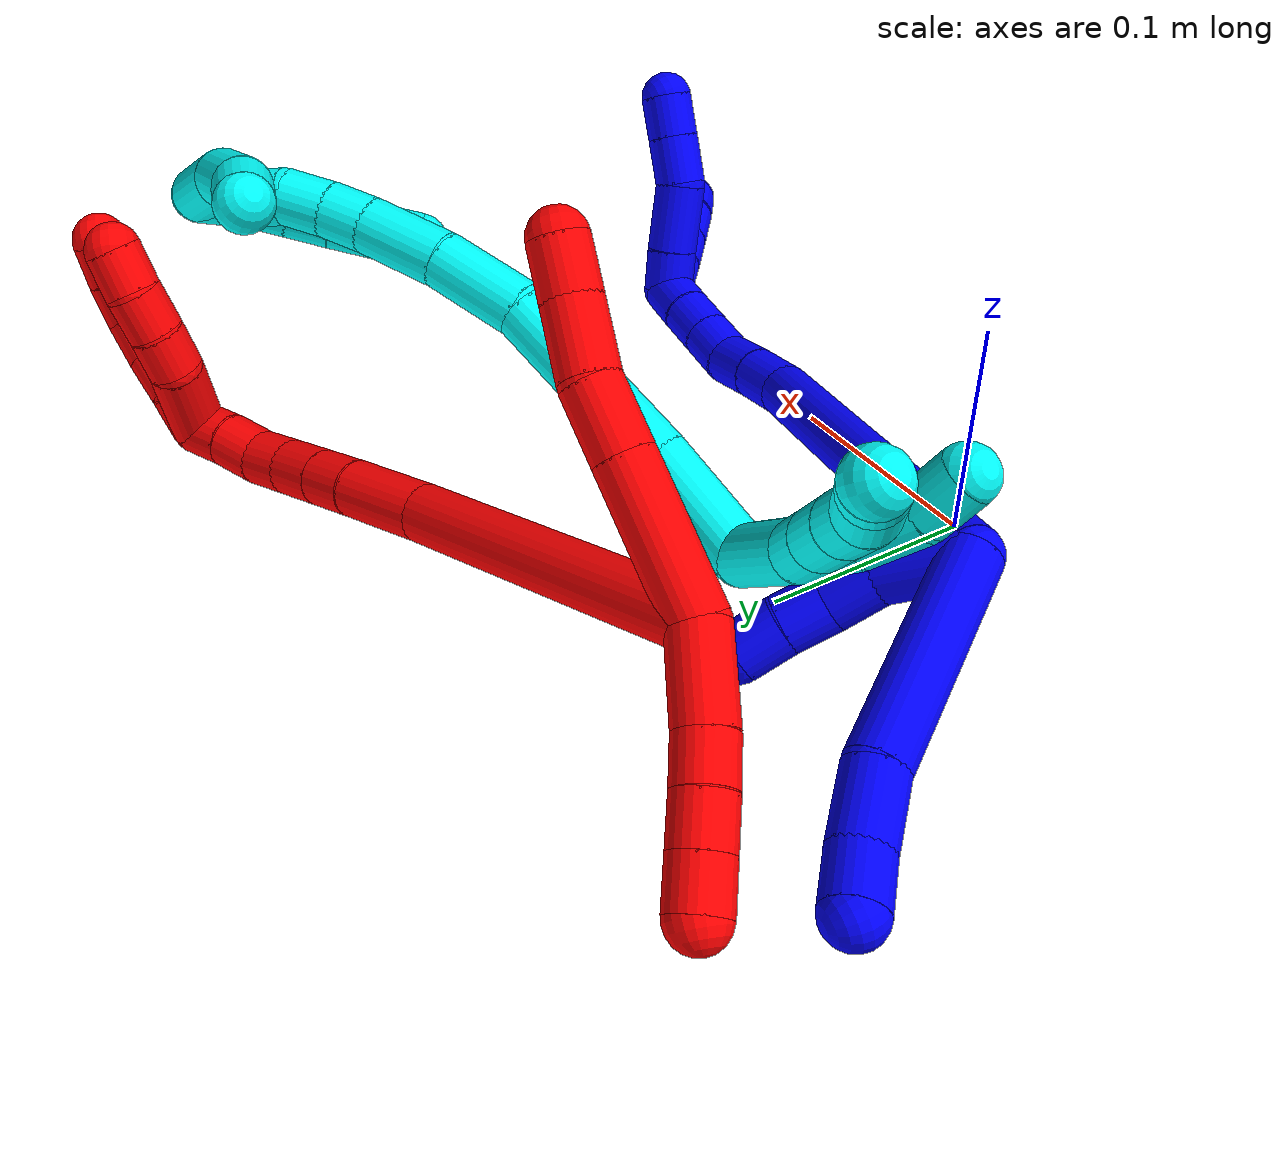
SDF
<sdf version="1.7">
 <world name="default">
  <plugin name="TubeGeneratorPlugin" filename="libtube_generator_plugin.so"/>
  <model name="photoneo_s_sensor">
   <static>1</static>
   <pose>0 0 2 1.57079 1.57079 3.14159</pose>
   <link name="link">
    <inertial><mass>0.1</mass></inertial>
    <sensor name="sensor" type="depth">
     <update_rate>30</update_rate>
     <camera>
      <horizontal_fov>1.22</horizontal_fov>
      <image><width>1920</width><height>1200</height><format>B8G8R8</format></image>
      <clip><near>0.1</near><far>4</far></clip>
      <depth_camera><output>points</output></depth_camera>
     </camera>
     <plugin name="camera_plugin" filename="libgazebo_ros_depth_camera.so">
      <baseline>0.2</baseline>
      <alwaysOn>1</alwaysOn>
      <updateRate>0.0</updateRate>
      <cameraName>camera_ir</cameraName>
      <imageTopicName>/camera/color/image_raw</imageTopicName>
      <cameraInfoTopicName>/camera/color/camera_info</cameraInfoTopicName>
      <depthImageTopicName>/camera/depth/image_raw</depthImageTopicName>
      <depthImageCameraInfoTopicName>/camera/depth/camera_info</depthImageCameraInfoTopicName>
      <pointCloudTopicName>/camera/depth/points</pointCloudTopicName>
      <frameName>fr_optical</frameName>
      <pointCloudCutoff>0.1</pointCloudCutoff>
      <pointCloudCutoffMax>2.0</pointCloudCutoffMax>
      <distortionK1>0</distortionK1>
      <distortionK2>0</distortionK2>
      <distortionK3>0</distortionK3>
      <distortionT1>0</distortionT1>
      <distortionT2>0</distortionT2>
      <CxPrime>0</CxPrime>
      <Cx>0</Cx>
      <Cy>0</Cy>
      <focalLength>0</focalLength>
      <hackBaseline>0</hackBaseline>
     </plugin>
    </sensor>
   </link>
  </model>
  <gravity>0 0 -9.8</gravity>
  <magnetic_field>6e-06 2.3e-05 -4.2e-05</magnetic_field>
  <atmosphere type="adiabatic"/>
  <physics name="default_physics" default="0" type="ode">
   <max_step_size>0.003</max_step_size>
   <real_time_factor>1</real_time_factor>
   <real_time_update_rate>1000</real_time_update_rate>
   <max_contacts>10000</max_contacts>
   <ode>
    <solver>
     <type>quick</type>
     <iters>100</iters>
     <sor>1.3</sor>
     <use_dynamic_moi_rescaling>0</use_dynamic_moi_rescaling>
    </solver>
    <constraints>
     <contact_max_correcting_vel>0</contact_max_correcting_vel>
     <contact_surface_layer>0.001</contact_surface_layer>
     <cfm>0</cfm>
     <erp>0.2</erp>
    </constraints>
   </ode>
  </physics>
  <scene><ambient>0.4 0.4 0.4 1</ambient><background>0.7 0.7 0.7 1</background><shadows>0</shadows></scene>
  <audio><device>default</device></audio>
  <spherical_coordinates>
   <surface_model>EARTH_WGS84</surface_model>
   <latitude_deg>0</latitude_deg>
   <longitude_deg>0</longitude_deg>
   <elevation>0</elevation>
   <heading_deg>0</heading_deg>
  </spherical_coordinates>
  <model name="bin">
   <static>1</static>
   <link name="bottom">
    <collision name="collision-bottom">
     <pose>0 0 -0.01 0 -0 0</pose>
     <geometry><box><size>0.8 0.6 0.02</size></box></geometry>
     <surface>
      <friction><ode><mu>100</mu><mu2>100</mu2></ode></friction>
      <contact><collide_bitmask>65535</collide_bitmask></contact>
     </surface>
    </collision>
   </link>
   <link name="west_wall">
    <collision name="collision-west_wall">
     <pose>-0.41 0 0.1 0 -0 0</pose>
     <geometry><box><size>0.02 0.6 0.2</size></box></geometry>
     <surface>
      <friction><ode><mu>100</mu><mu2>100</mu2></ode></friction>
      <contact><collide_bitmask>65535</collide_bitmask></contact>
     </surface>
    </collision>
   </link>
   <link name="east_wall">
    <collision name="collision-east_wall">
     <pose>0.41 0 0.1 0 -0 0</pose>
     <geometry><box><size>0.02 0.6 0.2</size></box></geometry>
     <surface>
      <friction><ode><mu>100</mu><mu2>100</mu2></ode></friction>
      <contact><collide_bitmask>65535</collide_bitmask></contact>
     </surface>
    </collision>
   </link>
   <link name="south_wall">
    <collision name="collision-south_wall">
     <pose>0 -0.31 0.1 0 -0 0</pose>
     <geometry><box><size>0.8 0.02 0.2</size></box></geometry>
     <surface>
      <friction><ode><mu>100</mu><mu2>100</mu2></ode></friction>
      <contact><collide_bitmask>65535</collide_bitmask></contact>
     </surface>
    </collision>
   </link>
   <link name="north_wall">
    <collision name="collision-north_wall">
     <pose>0 0.31 0.1 0 -0 0</pose>
     <geometry><box><size>0.8 0.02 0.2</size></box></geometry>
     <surface>
      <friction><ode><mu>100</mu><mu2>100</mu2></ode></friction>
      <contact><collide_bitmask>65535</collide_bitmask></contact>
     </surface>
    </collision>
   </link>
  </model>
  <model name="1">
   <static>0</static>
   <link name="1">
    <collision name="collision-cylinder-e_1_2_8">
     <pose>-0.015491 0.024906 0.03885 -0.570083 -0.323855 0.095661</pose>
     <geometry><cylinder><radius>0.0125</radius><length>0.097358</length></cylinder></geometry>
     <surface>
      <friction><ode><mu>1.16</mu><mu2>1.16</mu2><slip1>0</slip1><slip2>0</slip2></ode></friction>
      <contact><ode><kp>1e+06</kp><kd>1</kd><max_vel>0</max_vel><min_depth>0.001</min_depth></ode></contact>
     </surface>
    </collision>
    <visual name="visual-cylinder-e_1_2_8">
     <pose>-0.015491 0.024906 0.03885 -0.570083 -0.323855 0.095661</pose>
     <geometry><cylinder><radius>0.0125</radius><length>0.097358</length></cylinder></geometry>
     <material><ambient>0 0 1 1</ambient></material>
    </visual>
    <collision name="collision-cylinder-e_2_8_9">
     <pose>-0.035697 0.060251 0.087541 -0.814852 -0.317571 0.138</pose>
     <geometry><cylinder><radius>0.0125</radius><length>0.0302</length></cylinder></geometry>
     <surface>
      <friction><ode><mu>1.16</mu><mu2>1.16</mu2><slip1>0</slip1><slip2>0</slip2></ode></friction>
      <contact><ode><kp>1e+06</kp><kd>1</kd><max_vel>0</max_vel><min_depth>0.001</min_depth></ode></contact>
     </surface>
    </collision>
    <visual name="visual-cylinder-e_2_8_9">
     <pose>-0.035697 0.060251 0.087541 -0.814852 -0.317571 0.138</pose>
     <geometry><cylinder><radius>0.0125</radius><length>0.0302</length></cylinder></geometry>
     <material><ambient>0 0 1 1</ambient></material>
    </visual>
    <collision name="collision-cylinder-e_3_9_6">
     <pose>-0.045819 0.077765 0.104208 -0.803369 -0.502799 0.217336</pose>
     <geometry><cylinder><radius>0.0125</radius><length>0.022442</length></cylinder></geometry>
     <surface>
      <friction><ode><mu>1.16</mu><mu2>1.16</mu2><slip1>0</slip1><slip2>0</slip2></ode></friction>
      <contact><ode><kp>1e+06</kp><kd>1</kd><max_vel>0</max_vel><min_depth>0.001</min_depth></ode></contact>
     </surface>
    </collision>
    <visual name="visual-cylinder-e_3_9_6">
     <pose>-0.045819 0.077765 0.104208 -0.803369 -0.502799 0.217336</pose>
     <geometry><cylinder><radius>0.0125</radius><length>0.022442</length></cylinder></geometry>
     <material><ambient>0 0 1 1</ambient></material>
    </visual>
    <collision name="collision-cylinder-e_1_2_10">
     <pose>0.01291 -0.002465 0.01303 0.186995 0.771997 0.076177</pose>
     <geometry><cylinder><radius>0.0125</radius><length>0.037015</length></cylinder></geometry>
     <surface>
      <friction><ode><mu>1.16</mu><mu2>1.16</mu2><slip1>0</slip1><slip2>0</slip2></ode></friction>
      <contact><ode><kp>1e+06</kp><kd>1</kd><max_vel>0</max_vel><min_depth>0.001</min_depth></ode></contact>
     </surface>
    </collision>
    <visual name="visual-cylinder-e_1_2_10">
     <pose>0.01291 -0.002465 0.01303 0.186995 0.771997 0.076177</pose>
     <geometry><cylinder><radius>0.0125</radius><length>0.037015</length></cylinder></geometry>
     <material><ambient>0 0 1 1</ambient></material>
    </visual>
    <collision name="collision-cylinder-e_2_10_11">
     <pose>0.032133 -0.003115 0.035069 -0.19888 0.601834 -0.061905</pose>
     <geometry><cylinder><radius>0.0125</radius><length>0.0223</length></cylinder></geometry>
     <surface>
      <friction><ode><mu>1.16</mu><mu2>1.16</mu2><slip1>0</slip1><slip2>0</slip2></ode></friction>
      <contact><ode><kp>1e+06</kp><kd>1</kd><max_vel>0</max_vel><min_depth>0.001</min_depth></ode></contact>
     </surface>
    </collision>
    <visual name="visual-cylinder-e_2_10_11">
     <pose>0.032133 -0.003115 0.035069 -0.19888 0.601834 -0.061905</pose>
     <geometry><cylinder><radius>0.0125</radius><length>0.0223</length></cylinder></geometry>
     <material><ambient>0 0 1 1</ambient></material>
    </visual>
    <collision name="collision-cylinder-e_3_11_12">
     <pose>0.042526 -0.000275 0.053169 -0.112163 0.419547 -0.023904</pose>
     <geometry><cylinder><radius>0.0125</radius><length>0.020033</length></cylinder></geometry>
     <surface>
      <friction><ode><mu>1.16</mu><mu2>1.16</mu2><slip1>0</slip1><slip2>0</slip2></ode></friction>
      <contact><ode><kp>1e+06</kp><kd>1</kd><max_vel>0</max_vel><min_depth>0.001</min_depth></ode></contact>
     </surface>
    </collision>
    <visual name="visual-cylinder-e_3_11_12">
     <pose>0.042526 -0.000275 0.053169 -0.112163 0.419547 -0.023904</pose>
     <geometry><cylinder><radius>0.0125</radius><length>0.020033</length></cylinder></geometry>
     <material><ambient>0 0 1 1</ambient></material>
    </visual>
    <collision name="collision-cylinder-e_4_12_5">
     <pose>0.051206 0.002717 0.071292 -0.214578 0.461731 -0.050621</pose>
     <geometry><cylinder><radius>0.0125</radius><length>0.020653</length></cylinder></geometry>
     <surface>
      <friction><ode><mu>1.16</mu><mu2>1.16</mu2><slip1>0</slip1><slip2>0</slip2></ode></friction>
      <contact><ode><kp>1e+06</kp><kd>1</kd><max_vel>0</max_vel><min_depth>0.001</min_depth></ode></contact>
     </surface>
    </collision>
    <visual name="visual-cylinder-e_4_12_5">
     <pose>0.051206 0.002717 0.071292 -0.214578 0.461731 -0.050621</pose>
     <geometry><cylinder><radius>0.0125</radius><length>0.020653</length></cylinder></geometry>
     <material><ambient>0 0 1 1</ambient></material>
    </visual>
    <collision name="collision-cylinder-e_1_2_13">
     <pose>0.083445 -0.044527 -0.012601 1.84658 1.06445 1.32324</pose>
     <geometry><cylinder><radius>0.0125</radius><length>0.190834</length></cylinder></geometry>
     <surface>
      <friction><ode><mu>1.16</mu><mu2>1.16</mu2><slip1>0</slip1><slip2>0</slip2></ode></friction>
      <contact><ode><kp>1e+06</kp><kd>1</kd><max_vel>0</max_vel><min_depth>0.001</min_depth></ode></contact>
     </surface>
    </collision>
    <visual name="visual-cylinder-e_1_2_13">
     <pose>0.083445 -0.044527 -0.012601 1.84658 1.06445 1.32324</pose>
     <geometry><cylinder><radius>0.0125</radius><length>0.190834</length></cylinder></geometry>
     <material><ambient>0 0 1 1</ambient></material>
    </visual>
    <collision name="collision-cylinder-e_2_13_14">
     <pose>0.176316 -0.09591 -0.023891 1.38191 0.933424 0.789543</pose>
     <geometry><cylinder><radius>0.0125</radius><length>0.023459</length></cylinder></geometry>
     <surface>
      <friction><ode><mu>1.16</mu><mu2>1.16</mu2><slip1>0</slip1><slip2>0</slip2></ode></friction>
      <contact><ode><kp>1e+06</kp><kd>1</kd><max_vel>0</max_vel><min_depth>0.001</min_depth></ode></contact>
     </surface>
    </collision>
    <visual name="visual-cylinder-e_2_13_14">
     <pose>0.176316 -0.09591 -0.023891 1.38191 0.933424 0.789543</pose>
     <geometry><cylinder><radius>0.0125</radius><length>0.023459</length></cylinder></geometry>
     <material><ambient>0 0 1 1</ambient></material>
    </visual>
    <collision name="collision-cylinder-e_3_14_15">
     <pose>0.195504 -0.109106 -0.021187 1.35439 0.983881 0.813657</pose>
     <geometry><cylinder><radius>0.0125</radius><length>0.023447</length></cylinder></geometry>
     <surface>
      <friction><ode><mu>1.16</mu><mu2>1.16</mu2><slip1>0</slip1><slip2>0</slip2></ode></friction>
      <contact><ode><kp>1e+06</kp><kd>1</kd><max_vel>0</max_vel><min_depth>0.001</min_depth></ode></contact>
     </surface>
    </collision>
    <visual name="visual-cylinder-e_3_14_15">
     <pose>0.195504 -0.109106 -0.021187 1.35439 0.983881 0.813657</pose>
     <geometry><cylinder><radius>0.0125</radius><length>0.023447</length></cylinder></geometry>
     <material><ambient>0 0 1 1</ambient></material>
    </visual>
    <collision name="collision-cylinder-e_4_15_16">
     <pose>0.211563 -0.123522 -0.019413 1.52383 0.66182 0.633478</pose>
     <geometry><cylinder><radius>0.0125</radius><length>0.020494</length></cylinder></geometry>
     <surface>
      <friction><ode><mu>1.16</mu><mu2>1.16</mu2><slip1>0</slip1><slip2>0</slip2></ode></friction>
      <contact><ode><kp>1e+06</kp><kd>1</kd><max_vel>0</max_vel><min_depth>0.001</min_depth></ode></contact>
     </surface>
    </collision>
    <visual name="visual-cylinder-e_4_15_16">
     <pose>0.211563 -0.123522 -0.019413 1.52383 0.66182 0.633478</pose>
     <geometry><cylinder><radius>0.0125</radius><length>0.020494</length></cylinder></geometry>
     <material><ambient>0 0 1 1</ambient></material>
    </visual>
    <collision name="collision-cylinder-e_5_16_17">
     <pose>0.224154 -0.139649 -0.018647 1.52288 0.662856 0.633913</pose>
     <geometry><cylinder><radius>0.0125</radius><length>0.020456</length></cylinder></geometry>
     <surface>
      <friction><ode><mu>1.16</mu><mu2>1.16</mu2><slip1>0</slip1><slip2>0</slip2></ode></friction>
      <contact><ode><kp>1e+06</kp><kd>1</kd><max_vel>0</max_vel><min_depth>0.001</min_depth></ode></contact>
     </surface>
    </collision>
    <visual name="visual-cylinder-e_5_16_17">
     <pose>0.224154 -0.139649 -0.018647 1.52288 0.662856 0.633913</pose>
     <geometry><cylinder><radius>0.0125</radius><length>0.020456</length></cylinder></geometry>
     <material><ambient>0 0 1 1</ambient></material>
    </visual>
    <collision name="collision-cylinder-e_6_17_1">
     <pose>0.237454 -0.155729 -0.018363 1.58344 0.717521 0.725877</pose>
     <geometry><cylinder><radius>0.0125</radius><length>0.02131</length></cylinder></geometry>
     <surface>
      <friction><ode><mu>1.16</mu><mu2>1.16</mu2><slip1>0</slip1><slip2>0</slip2></ode></friction>
      <contact><ode><kp>1e+06</kp><kd>1</kd><max_vel>0</max_vel><min_depth>0.001</min_depth></ode></contact>
     </surface>
    </collision>
    <visual name="visual-cylinder-e_6_17_1">
     <pose>0.237454 -0.155729 -0.018363 1.58344 0.717521 0.725877</pose>
     <geometry><cylinder><radius>0.0125</radius><length>0.02131</length></cylinder></geometry>
     <material><ambient>0 0 1 1</ambient></material>
    </visual>
    <collision name="collision-cylinder-e_1_1_18">
     <pose>0.24 -0.172577 -0.021816 1.93392 -0.441505 -0.629063</pose>
     <geometry><cylinder><radius>0.0125</radius><length>0.020874</length></cylinder></geometry>
     <surface>
      <friction><ode><mu>1.16</mu><mu2>1.16</mu2><slip1>0</slip1><slip2>0</slip2></ode></friction>
      <contact><ode><kp>1e+06</kp><kd>1</kd><max_vel>0</max_vel><min_depth>0.001</min_depth></ode></contact>
     </surface>
    </collision>
    <visual name="visual-cylinder-e_1_1_18">
     <pose>0.24 -0.172577 -0.021816 1.93392 -0.441505 -0.629063</pose>
     <geometry><cylinder><radius>0.0125</radius><length>0.020874</length></cylinder></geometry>
     <material><ambient>0 0 1 1</ambient></material>
    </visual>
    <collision name="collision-cylinder-e_2_18_19">
     <pose>0.228461 -0.195511 -0.031409 1.98716 -0.430148 -0.647333</pose>
     <geometry><cylinder><radius>0.0125</radius><length>0.033955</length></cylinder></geometry>
     <surface>
      <friction><ode><mu>1.16</mu><mu2>1.16</mu2><slip1>0</slip1><slip2>0</slip2></ode></friction>
      <contact><ode><kp>1e+06</kp><kd>1</kd><max_vel>0</max_vel><min_depth>0.001</min_depth></ode></contact>
     </surface>
    </collision>
    <visual name="visual-cylinder-e_2_18_19">
     <pose>0.228461 -0.195511 -0.031409 1.98716 -0.430148 -0.647333</pose>
     <geometry><cylinder><radius>0.0125</radius><length>0.033955</length></cylinder></geometry>
     <material><ambient>0 0 1 1</ambient></material>
    </visual>
    <collision name="collision-cylinder-e_3_19_20">
     <pose>0.218951 -0.221263 -0.039636 1.73985 -0.20295 -0.240193</pose>
     <geometry><cylinder><radius>0.0125</radius><length>0.02411</length></cylinder></geometry>
     <surface>
      <friction><ode><mu>1.16</mu><mu2>1.16</mu2><slip1>0</slip1><slip2>0</slip2></ode></friction>
      <contact><ode><kp>1e+06</kp><kd>1</kd><max_vel>0</max_vel><min_depth>0.001</min_depth></ode></contact>
     </surface>
    </collision>
    <visual name="visual-cylinder-e_3_19_20">
     <pose>0.218951 -0.221263 -0.039636 1.73985 -0.20295 -0.240193</pose>
     <geometry><cylinder><radius>0.0125</radius><length>0.02411</length></cylinder></geometry>
     <material><ambient>0 0 1 1</ambient></material>
    </visual>
    <collision name="collision-cylinder-e_4_20_4">
     <pose>0.214417 -0.243084 -0.043295 1.7336 -0.201168 -0.236601</pose>
     <geometry><cylinder><radius>0.0125</radius><length>0.021061</length></cylinder></geometry>
     <surface>
      <friction><ode><mu>1.16</mu><mu2>1.16</mu2><slip1>0</slip1><slip2>0</slip2></ode></friction>
      <contact><ode><kp>1e+06</kp><kd>1</kd><max_vel>0</max_vel><min_depth>0.001</min_depth></ode></contact>
     </surface>
    </collision>
    <visual name="visual-cylinder-e_4_20_4">
     <pose>0.214417 -0.243084 -0.043295 1.7336 -0.201168 -0.236601</pose>
     <geometry><cylinder><radius>0.0125</radius><length>0.021061</length></cylinder></geometry>
     <material><ambient>0 0 1 1</ambient></material>
    </visual>
    <collision name="collision-cylinder-e_1_1_21">
     <pose>0.25156 -0.170139 -0.025509 2.40547 0.641487 1.42224</pose>
     <geometry><cylinder><radius>0.0125</radius><length>0.023731</length></cylinder></geometry>
     <surface>
      <friction><ode><mu>1.16</mu><mu2>1.16</mu2><slip1>0</slip1><slip2>0</slip2></ode></friction>
      <contact><ode><kp>1e+06</kp><kd>1</kd><max_vel>0</max_vel><min_depth>0.001</min_depth></ode></contact>
     </surface>
    </collision>
    <visual name="visual-cylinder-e_1_1_21">
     <pose>0.25156 -0.170139 -0.025509 2.40547 0.641487 1.42224</pose>
     <geometry><cylinder><radius>0.0125</radius><length>0.023731</length></cylinder></geometry>
     <material><ambient>0 0 1 1</ambient></material>
    </visual>
    <collision name="collision-cylinder-e_2_21_22">
     <pose>0.265883 -0.183142 -0.039618 2.3886 0.641039 1.39693</pose>
     <geometry><cylinder><radius>0.0125</radius><length>0.024156</length></cylinder></geometry>
     <surface>
      <friction><ode><mu>1.16</mu><mu2>1.16</mu2><slip1>0</slip1><slip2>0</slip2></ode></friction>
      <contact><ode><kp>1e+06</kp><kd>1</kd><max_vel>0</max_vel><min_depth>0.001</min_depth></ode></contact>
     </surface>
    </collision>
    <visual name="visual-cylinder-e_2_21_22">
     <pose>0.265883 -0.183142 -0.039618 2.3886 0.641039 1.39693</pose>
     <geometry><cylinder><radius>0.0125</radius><length>0.024156</length></cylinder></geometry>
     <material><ambient>0 0 1 1</ambient></material>
    </visual>
    <collision name="collision-cylinder-e_3_22_23">
     <pose>0.281147 -0.197044 -0.054434 2.38753 0.647302 1.40566</pose>
     <geometry><cylinder><radius>0.0125</radius><length>0.026668</length></cylinder></geometry>
     <surface>
      <friction><ode><mu>1.16</mu><mu2>1.16</mu2><slip1>0</slip1><slip2>0</slip2></ode></friction>
      <contact><ode><kp>1e+06</kp><kd>1</kd><max_vel>0</max_vel><min_depth>0.001</min_depth></ode></contact>
     </surface>
    </collision>
    <visual name="visual-cylinder-e_3_22_23">
     <pose>0.281147 -0.197044 -0.054434 2.38753 0.647302 1.40566</pose>
     <geometry><cylinder><radius>0.0125</radius><length>0.026668</length></cylinder></geometry>
     <material><ambient>0 0 1 1</ambient></material>
    </visual>
    <collision name="collision-cylinder-e_4_23_3">
     <pose>0.298364 -0.21029 -0.068675 2.39823 0.805614 1.65973</pose>
     <geometry><cylinder><radius>0.0125</radius><length>0.025445</length></cylinder></geometry>
     <surface>
      <friction><ode><mu>1.16</mu><mu2>1.16</mu2><slip1>0</slip1><slip2>0</slip2></ode></friction>
      <contact><ode><kp>1e+06</kp><kd>1</kd><max_vel>0</max_vel><min_depth>0.001</min_depth></ode></contact>
     </surface>
    </collision>
    <visual name="visual-cylinder-e_4_23_3">
     <pose>0.298364 -0.21029 -0.068675 2.39823 0.805614 1.65973</pose>
     <geometry><cylinder><radius>0.0125</radius><length>0.025445</length></cylinder></geometry>
     <material><ambient>0 0 1 1</ambient></material>
    </visual>
    <collision name="collision-sphere-3">
     <pose>0.30754 -0.216254 -0.075163 0 -0 0</pose>
     <geometry><sphere><radius>0.0125</radius></sphere></geometry>
     <surface>
      <friction><ode><mu>1.16</mu><mu2>1.16</mu2><slip1>0</slip1><slip2>0</slip2></ode></friction>
      <contact><ode><kp>1e+06</kp><kd>1</kd><max_vel>0</max_vel><min_depth>0.001</min_depth></ode></contact>
     </surface>
    </collision>
    <visual name="visual-sphere-3">
     <pose>0.30754 -0.216254 -0.075163 0 -0 0</pose>
     <geometry><sphere><radius>0.0125</radius></sphere></geometry>
     <material><ambient>0 0 1 1</ambient></material>
    </visual>
    <collision name="collision-sphere-23">
     <pose>0.289188 -0.204326 -0.062187 0 -0 0</pose>
     <geometry><sphere><radius>0.0125</radius></sphere></geometry>
     <surface>
      <friction><ode><mu>1.16</mu><mu2>1.16</mu2><slip1>0</slip1><slip2>0</slip2></ode></friction>
      <contact><ode><kp>1e+06</kp><kd>1</kd><max_vel>0</max_vel><min_depth>0.001</min_depth></ode></contact>
     </surface>
    </collision>
    <visual name="visual-sphere-23">
     <pose>0.289188 -0.204326 -0.062187 0 -0 0</pose>
     <geometry><sphere><radius>0.0125</radius></sphere></geometry>
     <material><ambient>0 0 1 1</ambient></material>
    </visual>
    <collision name="collision-sphere-22">
     <pose>0.273106 -0.189762 -0.046681 0 -0 0</pose>
     <geometry><sphere><radius>0.0125</radius></sphere></geometry>
     <surface>
      <friction><ode><mu>1.16</mu><mu2>1.16</mu2><slip1>0</slip1><slip2>0</slip2></ode></friction>
      <contact><ode><kp>1e+06</kp><kd>1</kd><max_vel>0</max_vel><min_depth>0.001</min_depth></ode></contact>
     </surface>
    </collision>
    <visual name="visual-sphere-22">
     <pose>0.273106 -0.189762 -0.046681 0 -0 0</pose>
     <geometry><sphere><radius>0.0125</radius></sphere></geometry>
     <material><ambient>0 0 1 1</ambient></material>
    </visual>
    <collision name="collision-sphere-21">
     <pose>0.25866 -0.176522 -0.032554 0 -0 0</pose>
     <geometry><sphere><radius>0.0125</radius></sphere></geometry>
     <surface>
      <friction><ode><mu>1.16</mu><mu2>1.16</mu2><slip1>0</slip1><slip2>0</slip2></ode></friction>
      <contact><ode><kp>1e+06</kp><kd>1</kd><max_vel>0</max_vel><min_depth>0.001</min_depth></ode></contact>
     </surface>
    </collision>
    <visual name="visual-sphere-21">
     <pose>0.25866 -0.176522 -0.032554 0 -0 0</pose>
     <geometry><sphere><radius>0.0125</radius></sphere></geometry>
     <material><ambient>0 0 1 1</ambient></material>
    </visual>
    <collision name="collision-sphere-4">
     <pose>0.212313 -0.253265 -0.044968 0 -0 0</pose>
     <geometry><sphere><radius>0.0125</radius></sphere></geometry>
     <surface>
      <friction><ode><mu>1.16</mu><mu2>1.16</mu2><slip1>0</slip1><slip2>0</slip2></ode></friction>
      <contact><ode><kp>1e+06</kp><kd>1</kd><max_vel>0</max_vel><min_depth>0.001</min_depth></ode></contact>
     </surface>
    </collision>
    <visual name="visual-sphere-4">
     <pose>0.212313 -0.253265 -0.044968 0 -0 0</pose>
     <geometry><sphere><radius>0.0125</radius></sphere></geometry>
     <material><ambient>0 0 1 1</ambient></material>
    </visual>
    <collision name="collision-sphere-20">
     <pose>0.216521 -0.232902 -0.041623 0 -0 0</pose>
     <geometry><sphere><radius>0.0125</radius></sphere></geometry>
     <surface>
      <friction><ode><mu>1.16</mu><mu2>1.16</mu2><slip1>0</slip1><slip2>0</slip2></ode></friction>
      <contact><ode><kp>1e+06</kp><kd>1</kd><max_vel>0</max_vel><min_depth>0.001</min_depth></ode></contact>
     </surface>
    </collision>
    <visual name="visual-sphere-20">
     <pose>0.216521 -0.232902 -0.041623 0 -0 0</pose>
     <geometry><sphere><radius>0.0125</radius></sphere></geometry>
     <material><ambient>0 0 1 1</ambient></material>
    </visual>
    <collision name="collision-sphere-11">
     <pose>0.038445 -0.001299 0.044079 0 -0 0</pose>
     <geometry><sphere><radius>0.0125</radius></sphere></geometry>
     <surface>
      <friction><ode><mu>1.16</mu><mu2>1.16</mu2><slip1>0</slip1><slip2>0</slip2></ode></friction>
      <contact><ode><kp>1e+06</kp><kd>1</kd><max_vel>0</max_vel><min_depth>0.001</min_depth></ode></contact>
     </surface>
    </collision>
    <visual name="visual-sphere-11">
     <pose>0.038445 -0.001299 0.044079 0 -0 0</pose>
     <geometry><sphere><radius>0.0125</radius></sphere></geometry>
     <material><ambient>0 0 1 1</ambient></material>
    </visual>
    <collision name="collision-sphere-10">
     <pose>0.02582 -0.004931 0.026059 0 -0 0</pose>
     <geometry><sphere><radius>0.0125</radius></sphere></geometry>
     <surface>
      <friction><ode><mu>1.16</mu><mu2>1.16</mu2><slip1>0</slip1><slip2>0</slip2></ode></friction>
      <contact><ode><kp>1e+06</kp><kd>1</kd><max_vel>0</max_vel><min_depth>0.001</min_depth></ode></contact>
     </surface>
    </collision>
    <visual name="visual-sphere-10">
     <pose>0.02582 -0.004931 0.026059 0 -0 0</pose>
     <geometry><sphere><radius>0.0125</radius></sphere></geometry>
     <material><ambient>0 0 1 1</ambient></material>
    </visual>
    <collision name="collision-sphere-6">
     <pose>-0.051226 0.084841 0.111034 0 -0 0</pose>
     <geometry><sphere><radius>0.0125</radius></sphere></geometry>
     <surface>
      <friction><ode><mu>1.16</mu><mu2>1.16</mu2><slip1>0</slip1><slip2>0</slip2></ode></friction>
      <contact><ode><kp>1e+06</kp><kd>1</kd><max_vel>0</max_vel><min_depth>0.001</min_depth></ode></contact>
     </surface>
    </collision>
    <visual name="visual-sphere-6">
     <pose>-0.051226 0.084841 0.111034 0 -0 0</pose>
     <geometry><sphere><radius>0.0125</radius></sphere></geometry>
     <material><ambient>0 0 1 1</ambient></material>
    </visual>
    <collision name="collision-sphere-9">
     <pose>-0.040412 0.070688 0.097381 0 -0 0</pose>
     <geometry><sphere><radius>0.0125</radius></sphere></geometry>
     <surface>
      <friction><ode><mu>1.16</mu><mu2>1.16</mu2><slip1>0</slip1><slip2>0</slip2></ode></friction>
      <contact><ode><kp>1e+06</kp><kd>1</kd><max_vel>0</max_vel><min_depth>0.001</min_depth></ode></contact>
     </surface>
    </collision>
    <visual name="visual-sphere-9">
     <pose>-0.040412 0.070688 0.097381 0 -0 0</pose>
     <geometry><sphere><radius>0.0125</radius></sphere></geometry>
     <material><ambient>0 0 1 1</ambient></material>
    </visual>
    <collision name="collision-sphere-2">
     <geometry><sphere><radius>0.0125</radius></sphere></geometry>
     <surface>
      <friction><ode><mu>1.16</mu><mu2>1.16</mu2><slip1>0</slip1><slip2>0</slip2></ode></friction>
      <contact><ode><kp>1e+06</kp><kd>1</kd><max_vel>0</max_vel><min_depth>0.001</min_depth></ode></contact>
     </surface>
    </collision>
    <visual name="visual-sphere-2">
     <geometry><sphere><radius>0.0125</radius></sphere></geometry>
     <material><ambient>0 0 1 1</ambient></material>
    </visual>
    <collision name="collision-sphere-19">
     <pose>0.221381 -0.209624 -0.037649 0 -0 0</pose>
     <geometry><sphere><radius>0.0125</radius></sphere></geometry>
     <surface>
      <friction><ode><mu>1.16</mu><mu2>1.16</mu2><slip1>0</slip1><slip2>0</slip2></ode></friction>
      <contact><ode><kp>1e+06</kp><kd>1</kd><max_vel>0</max_vel><min_depth>0.001</min_depth></ode></contact>
     </surface>
    </collision>
    <visual name="visual-sphere-19">
     <pose>0.221381 -0.209624 -0.037649 0 -0 0</pose>
     <geometry><sphere><radius>0.0125</radius></sphere></geometry>
     <material><ambient>0 0 1 1</ambient></material>
    </visual>
    <collision name="collision-sphere-8">
     <pose>-0.030981 0.049813 0.0777 0 -0 0</pose>
     <geometry><sphere><radius>0.0125</radius></sphere></geometry>
     <surface>
      <friction><ode><mu>1.16</mu><mu2>1.16</mu2><slip1>0</slip1><slip2>0</slip2></ode></friction>
      <contact><ode><kp>1e+06</kp><kd>1</kd><max_vel>0</max_vel><min_depth>0.001</min_depth></ode></contact>
     </surface>
    </collision>
    <visual name="visual-sphere-8">
     <pose>-0.030981 0.049813 0.0777 0 -0 0</pose>
     <geometry><sphere><radius>0.0125</radius></sphere></geometry>
     <material><ambient>0 0 1 1</ambient></material>
    </visual>
    <collision name="collision-sphere-12">
     <pose>0.046606 0.000749 0.062259 0 -0 0</pose>
     <geometry><sphere><radius>0.0125</radius></sphere></geometry>
     <surface>
      <friction><ode><mu>1.16</mu><mu2>1.16</mu2><slip1>0</slip1><slip2>0</slip2></ode></friction>
      <contact><ode><kp>1e+06</kp><kd>1</kd><max_vel>0</max_vel><min_depth>0.001</min_depth></ode></contact>
     </surface>
    </collision>
    <visual name="visual-sphere-12">
     <pose>0.046606 0.000749 0.062259 0 -0 0</pose>
     <geometry><sphere><radius>0.0125</radius></sphere></geometry>
     <material><ambient>0 0 1 1</ambient></material>
    </visual>
    <collision name="collision-sphere-5">
     <pose>0.055806 0.004686 0.080325 0 -0 0</pose>
     <geometry><sphere><radius>0.0125</radius></sphere></geometry>
     <surface>
      <friction><ode><mu>1.16</mu><mu2>1.16</mu2><slip1>0</slip1><slip2>0</slip2></ode></friction>
      <contact><ode><kp>1e+06</kp><kd>1</kd><max_vel>0</max_vel><min_depth>0.001</min_depth></ode></contact>
     </surface>
    </collision>
    <visual name="visual-sphere-5">
     <pose>0.055806 0.004686 0.080325 0 -0 0</pose>
     <geometry><sphere><radius>0.0125</radius></sphere></geometry>
     <material><ambient>0 0 1 1</ambient></material>
    </visual>
    <collision name="collision-sphere-13">
     <pose>0.16689 -0.089054 -0.025202 0 -0 0</pose>
     <geometry><sphere><radius>0.0125</radius></sphere></geometry>
     <surface>
      <friction><ode><mu>1.16</mu><mu2>1.16</mu2><slip1>0</slip1><slip2>0</slip2></ode></friction>
      <contact><ode><kp>1e+06</kp><kd>1</kd><max_vel>0</max_vel><min_depth>0.001</min_depth></ode></contact>
     </surface>
    </collision>
    <visual name="visual-sphere-13">
     <pose>0.16689 -0.089054 -0.025202 0 -0 0</pose>
     <geometry><sphere><radius>0.0125</radius></sphere></geometry>
     <material><ambient>0 0 1 1</ambient></material>
    </visual>
    <collision name="collision-sphere-14">
     <pose>0.185743 -0.102765 -0.022581 0 -0 0</pose>
     <geometry><sphere><radius>0.0125</radius></sphere></geometry>
     <surface>
      <friction><ode><mu>1.16</mu><mu2>1.16</mu2><slip1>0</slip1><slip2>0</slip2></ode></friction>
      <contact><ode><kp>1e+06</kp><kd>1</kd><max_vel>0</max_vel><min_depth>0.001</min_depth></ode></contact>
     </surface>
    </collision>
    <visual name="visual-sphere-14">
     <pose>0.185743 -0.102765 -0.022581 0 -0 0</pose>
     <geometry><sphere><radius>0.0125</radius></sphere></geometry>
     <material><ambient>0 0 1 1</ambient></material>
    </visual>
    <collision name="collision-sphere-15">
     <pose>0.205266 -0.115447 -0.019793 0 -0 0</pose>
     <geometry><sphere><radius>0.0125</radius></sphere></geometry>
     <surface>
      <friction><ode><mu>1.16</mu><mu2>1.16</mu2><slip1>0</slip1><slip2>0</slip2></ode></friction>
      <contact><ode><kp>1e+06</kp><kd>1</kd><max_vel>0</max_vel><min_depth>0.001</min_depth></ode></contact>
     </surface>
    </collision>
    <visual name="visual-sphere-15">
     <pose>0.205266 -0.115447 -0.019793 0 -0 0</pose>
     <geometry><sphere><radius>0.0125</radius></sphere></geometry>
     <material><ambient>0 0 1 1</ambient></material>
    </visual>
    <collision name="collision-sphere-16">
     <pose>0.217861 -0.131597 -0.019034 0 -0 0</pose>
     <geometry><sphere><radius>0.0125</radius></sphere></geometry>
     <surface>
      <friction><ode><mu>1.16</mu><mu2>1.16</mu2><slip1>0</slip1><slip2>0</slip2></ode></friction>
      <contact><ode><kp>1e+06</kp><kd>1</kd><max_vel>0</max_vel><min_depth>0.001</min_depth></ode></contact>
     </surface>
    </collision>
    <visual name="visual-sphere-16">
     <pose>0.217861 -0.131597 -0.019034 0 -0 0</pose>
     <geometry><sphere><radius>0.0125</radius></sphere></geometry>
     <material><ambient>0 0 1 1</ambient></material>
    </visual>
    <collision name="collision-sphere-17">
     <pose>0.230448 -0.147702 -0.018261 0 -0 0</pose>
     <geometry><sphere><radius>0.0125</radius></sphere></geometry>
     <surface>
      <friction><ode><mu>1.16</mu><mu2>1.16</mu2><slip1>0</slip1><slip2>0</slip2></ode></friction>
      <contact><ode><kp>1e+06</kp><kd>1</kd><max_vel>0</max_vel><min_depth>0.001</min_depth></ode></contact>
     </surface>
    </collision>
    <visual name="visual-sphere-17">
     <pose>0.230448 -0.147702 -0.018261 0 -0 0</pose>
     <geometry><sphere><radius>0.0125</radius></sphere></geometry>
     <material><ambient>0 0 1 1</ambient></material>
    </visual>
    <collision name="collision-sphere-1">
     <pose>0.24446 -0.163757 -0.018464 0 -0 0</pose>
     <geometry><sphere><radius>0.0125</radius></sphere></geometry>
     <surface>
      <friction><ode><mu>1.16</mu><mu2>1.16</mu2><slip1>0</slip1><slip2>0</slip2></ode></friction>
      <contact><ode><kp>1e+06</kp><kd>1</kd><max_vel>0</max_vel><min_depth>0.001</min_depth></ode></contact>
     </surface>
    </collision>
    <visual name="visual-sphere-1">
     <pose>0.24446 -0.163757 -0.018464 0 -0 0</pose>
     <geometry><sphere><radius>0.0125</radius></sphere></geometry>
     <material><ambient>0 0 1 1</ambient></material>
    </visual>
    <collision name="collision-sphere-18">
     <pose>0.23554 -0.181398 -0.025168 0 -0 0</pose>
     <geometry><sphere><radius>0.0125</radius></sphere></geometry>
     <surface>
      <friction><ode><mu>1.16</mu><mu2>1.16</mu2><slip1>0</slip1><slip2>0</slip2></ode></friction>
      <contact><ode><kp>1e+06</kp><kd>1</kd><max_vel>0</max_vel><min_depth>0.001</min_depth></ode></contact>
     </surface>
    </collision>
    <visual name="visual-sphere-18">
     <pose>0.23554 -0.181398 -0.025168 0 -0 0</pose>
     <geometry><sphere><radius>0.0125</radius></sphere></geometry>
     <material><ambient>0 0 1 1</ambient></material>
    </visual>
    <inertial>
     <pose>0.117545 -0.074527 -0.000289 0 -0 0</pose>
     <mass>0.75</mass>
     <inertia>
      <ixx>0.000485</ixx>
      <ixy>0</ixy>
      <ixz>0</ixz>
      <iyy>0.000803</iyy>
      <iyz>0</iyz>
      <izz>-0.000245</izz>
     </inertia>
    </inertial>
   </link>
   <pose>-0.074166 0.07197 0.064122 -1.76807 0.739486 -0.266492</pose>
  </model>
  <model name="2">
   <static>0</static>
   <link name="2">
    <collision name="collision-cylinder-e_1_2_8">
     <pose>-0.001099 -0.009051 -0.030658 2.85454 -0.034361 -0.236669</pose>
     <geometry><cylinder><radius>0.0125</radius><length>0.06397</length></cylinder></geometry>
     <surface>
      <friction><ode><mu>1.16</mu><mu2>1.16</mu2><slip1>0</slip1><slip2>0</slip2></ode></friction>
      <contact><ode><kp>1e+06</kp><kd>1</kd><max_vel>0</max_vel><min_depth>0.001</min_depth></ode></contact>
     </surface>
    </collision>
    <visual name="visual-cylinder-e_1_2_8">
     <pose>-0.001099 -0.009051 -0.030658 2.85454 -0.034361 -0.236669</pose>
     <geometry><cylinder><radius>0.0125</radius><length>0.06397</length></cylinder></geometry>
     <material><ambient>1 0 0 1</ambient></material>
    </visual>
    <collision name="collision-cylinder-e_2_8_9">
     <pose>-0.002717 -0.022327 -0.07567 2.85525 -0.034727 -0.239768</pose>
     <geometry><cylinder><radius>0.0125</radius><length>0.029943</length></cylinder></geometry>
     <surface>
      <friction><ode><mu>1.16</mu><mu2>1.16</mu2><slip1>0</slip1><slip2>0</slip2></ode></friction>
      <contact><ode><kp>1e+06</kp><kd>1</kd><max_vel>0</max_vel><min_depth>0.001</min_depth></ode></contact>
     </surface>
    </collision>
    <visual name="visual-cylinder-e_2_8_9">
     <pose>-0.002717 -0.022327 -0.07567 2.85525 -0.034727 -0.239768</pose>
     <geometry><cylinder><radius>0.0125</radius><length>0.029943</length></cylinder></geometry>
     <material><ambient>1 0 0 1</ambient></material>
    </visual>
    <collision name="collision-cylinder-e_3_9_10">
     <pose>-0.004088 -0.027589 -0.105888 3.0764 -0.05345 -1.37343</pose>
     <geometry><cylinder><radius>0.0125</radius><length>0.031841</length></cylinder></geometry>
     <surface>
      <friction><ode><mu>1.16</mu><mu2>1.16</mu2><slip1>0</slip1><slip2>0</slip2></ode></friction>
      <contact><ode><kp>1e+06</kp><kd>1</kd><max_vel>0</max_vel><min_depth>0.001</min_depth></ode></contact>
     </surface>
    </collision>
    <visual name="visual-cylinder-e_3_9_10">
     <pose>-0.004088 -0.027589 -0.105888 3.0764 -0.05345 -1.37343</pose>
     <geometry><cylinder><radius>0.0125</radius><length>0.031841</length></cylinder></geometry>
     <material><ambient>1 0 0 1</ambient></material>
    </visual>
    <collision name="collision-cylinder-e_4_10_6">
     <pose>-0.00748 -0.03056 -0.133446 2.97762 -0.211266 -1.82299</pose>
     <geometry><cylinder><radius>0.0125</radius><length>0.024245</length></cylinder></geometry>
     <surface>
      <friction><ode><mu>1.16</mu><mu2>1.16</mu2><slip1>0</slip1><slip2>0</slip2></ode></friction>
      <contact><ode><kp>1e+06</kp><kd>1</kd><max_vel>0</max_vel><min_depth>0.001</min_depth></ode></contact>
     </surface>
    </collision>
    <visual name="visual-cylinder-e_4_10_6">
     <pose>-0.00748 -0.03056 -0.133446 2.97762 -0.211266 -1.82299</pose>
     <geometry><cylinder><radius>0.0125</radius><length>0.024245</length></cylinder></geometry>
     <material><ambient>1 0 0 1</ambient></material>
    </visual>
    <collision name="collision-cylinder-e_1_2_11">
     <pose>0.000704 -0.002441 0.019232 0.126237 0.036302 0.002295</pose>
     <geometry><cylinder><radius>0.0125</radius><length>0.038799</length></cylinder></geometry>
     <surface>
      <friction><ode><mu>1.16</mu><mu2>1.16</mu2><slip1>0</slip1><slip2>0</slip2></ode></friction>
      <contact><ode><kp>1e+06</kp><kd>1</kd><max_vel>0</max_vel><min_depth>0.001</min_depth></ode></contact>
     </surface>
    </collision>
    <visual name="visual-cylinder-e_1_2_11">
     <pose>0.000704 -0.002441 0.019232 0.126237 0.036302 0.002295</pose>
     <geometry><cylinder><radius>0.0125</radius><length>0.038799</length></cylinder></geometry>
     <material><ambient>1 0 0 1</ambient></material>
    </visual>
    <collision name="collision-cylinder-e_2_11_12">
     <pose>0.001757 -0.007181 0.048277 0.230177 0.034644 0.004005</pose>
     <geometry><cylinder><radius>0.0125</radius><length>0.020168</length></cylinder></geometry>
     <surface>
      <friction><ode><mu>1.16</mu><mu2>1.16</mu2><slip1>0</slip1><slip2>0</slip2></ode></friction>
      <contact><ode><kp>1e+06</kp><kd>1</kd><max_vel>0</max_vel><min_depth>0.001</min_depth></ode></contact>
     </surface>
    </collision>
    <visual name="visual-cylinder-e_2_11_12">
     <pose>0.001757 -0.007181 0.048277 0.230177 0.034644 0.004005</pose>
     <geometry><cylinder><radius>0.0125</radius><length>0.020168</length></cylinder></geometry>
     <material><ambient>1 0 0 1</ambient></material>
    </visual>
    <collision name="collision-cylinder-e_3_12_13">
     <pose>0.003053 -0.011861 0.068028 0.235152 0.092291 0.010909</pose>
     <geometry><cylinder><radius>0.0125</radius><length>0.020528</length></cylinder></geometry>
     <surface>
      <friction><ode><mu>1.16</mu><mu2>1.16</mu2><slip1>0</slip1><slip2>0</slip2></ode></friction>
      <contact><ode><kp>1e+06</kp><kd>1</kd><max_vel>0</max_vel><min_depth>0.001</min_depth></ode></contact>
     </surface>
    </collision>
    <visual name="visual-cylinder-e_3_12_13">
     <pose>0.003053 -0.011861 0.068028 0.235152 0.092291 0.010909</pose>
     <geometry><cylinder><radius>0.0125</radius><length>0.020528</length></cylinder></geometry>
     <material><ambient>1 0 0 1</ambient></material>
    </visual>
    <collision name="collision-cylinder-e_4_13_5">
     <pose>0.004968 -0.016624 0.087892 0.235458 0.094701 0.011209</pose>
     <geometry><cylinder><radius>0.0125</radius><length>0.020505</length></cylinder></geometry>
     <surface>
      <friction><ode><mu>1.16</mu><mu2>1.16</mu2><slip1>0</slip1><slip2>0</slip2></ode></friction>
      <contact><ode><kp>1e+06</kp><kd>1</kd><max_vel>0</max_vel><min_depth>0.001</min_depth></ode></contact>
     </surface>
    </collision>
    <visual name="visual-cylinder-e_4_13_5">
     <pose>0.004968 -0.016624 0.087892 0.235458 0.094701 0.011209</pose>
     <geometry><cylinder><radius>0.0125</radius><length>0.020505</length></cylinder></geometry>
     <material><ambient>1 0 0 1</ambient></material>
    </visual>
    <collision name="collision-cylinder-e_1_2_14">
     <pose>0.058619 -0.02341 -0.042469 2.6378 0.879644 2.14064</pose>
     <geometry><cylinder><radius>0.0125</radius><length>0.152155</length></cylinder></geometry>
     <surface>
      <friction><ode><mu>1.16</mu><mu2>1.16</mu2><slip1>0</slip1><slip2>0</slip2></ode></friction>
      <contact><ode><kp>1e+06</kp><kd>1</kd><max_vel>0</max_vel><min_depth>0.001</min_depth></ode></contact>
     </surface>
    </collision>
    <visual name="visual-cylinder-e_1_2_14">
     <pose>0.058619 -0.02341 -0.042469 2.6378 0.879644 2.14064</pose>
     <geometry><cylinder><radius>0.0125</radius><length>0.152155</length></cylinder></geometry>
     <material><ambient>1 0 0 1</ambient></material>
    </visual>
    <collision name="collision-cylinder-e_2_14_15">
     <pose>0.132 -0.05543 -0.096173 2.48775 0.806431 1.79837</pose>
     <geometry><cylinder><radius>0.0125</radius><length>0.040903</length></cylinder></geometry>
     <surface>
      <friction><ode><mu>1.16</mu><mu2>1.16</mu2><slip1>0</slip1><slip2>0</slip2></ode></friction>
      <contact><ode><kp>1e+06</kp><kd>1</kd><max_vel>0</max_vel><min_depth>0.001</min_depth></ode></contact>
     </surface>
    </collision>
    <visual name="visual-cylinder-e_2_14_15">
     <pose>0.132 -0.05543 -0.096173 2.48775 0.806431 1.79837</pose>
     <geometry><cylinder><radius>0.0125</radius><length>0.040903</length></cylinder></geometry>
     <material><ambient>1 0 0 1</ambient></material>
    </visual>
    <collision name="collision-cylinder-e_3_15_16">
     <pose>0.155422 -0.067852 -0.113328 2.56934 0.888044 2.03383</pose>
     <geometry><cylinder><radius>0.0125</radius><length>0.022324</length></cylinder></geometry>
     <surface>
      <friction><ode><mu>1.16</mu><mu2>1.16</mu2><slip1>0</slip1><slip2>0</slip2></ode></friction>
      <contact><ode><kp>1e+06</kp><kd>1</kd><max_vel>0</max_vel><min_depth>0.001</min_depth></ode></contact>
     </surface>
    </collision>
    <visual name="visual-cylinder-e_3_15_16">
     <pose>0.155422 -0.067852 -0.113328 2.56934 0.888044 2.03383</pose>
     <geometry><cylinder><radius>0.0125</radius><length>0.022324</length></cylinder></geometry>
     <material><ambient>1 0 0 1</ambient></material>
    </visual>
    <collision name="collision-cylinder-e_4_16_17">
     <pose>0.173275 -0.07553 -0.12543 2.58293 0.900373 2.07034</pose>
     <geometry><cylinder><radius>0.0125</radius><length>0.023466</length></cylinder></geometry>
     <surface>
      <friction><ode><mu>1.16</mu><mu2>1.16</mu2><slip1>0</slip1><slip2>0</slip2></ode></friction>
      <contact><ode><kp>1e+06</kp><kd>1</kd><max_vel>0</max_vel><min_depth>0.001</min_depth></ode></contact>
     </surface>
    </collision>
    <visual name="visual-cylinder-e_4_16_17">
     <pose>0.173275 -0.07553 -0.12543 2.58293 0.900373 2.07034</pose>
     <geometry><cylinder><radius>0.0125</radius><length>0.023466</length></cylinder></geometry>
     <material><ambient>1 0 0 1</ambient></material>
    </visual>
    <collision name="collision-cylinder-e_5_17_18">
     <pose>0.190039 -0.083695 -0.137041 2.47174 0.829772 1.80414</pose>
     <geometry><cylinder><radius>0.0125</radius><length>0.020522</length></cylinder></geometry>
     <surface>
      <friction><ode><mu>1.16</mu><mu2>1.16</mu2><slip1>0</slip1><slip2>0</slip2></ode></friction>
      <contact><ode><kp>1e+06</kp><kd>1</kd><max_vel>0</max_vel><min_depth>0.001</min_depth></ode></contact>
     </surface>
    </collision>
    <visual name="visual-cylinder-e_5_17_18">
     <pose>0.190039 -0.083695 -0.137041 2.47174 0.829772 1.80414</pose>
     <geometry><cylinder><radius>0.0125</radius><length>0.020522</length></cylinder></geometry>
     <material><ambient>1 0 0 1</ambient></material>
    </visual>
    <collision name="collision-cylinder-e_6_18_19">
     <pose>0.203129 -0.093332 -0.148992 2.45569 0.579922 1.39218</pose>
     <geometry><cylinder><radius>0.0125</radius><length>0.020146</length></cylinder></geometry>
     <surface>
      <friction><ode><mu>1.16</mu><mu2>1.16</mu2><slip1>0</slip1><slip2>0</slip2></ode></friction>
      <contact><ode><kp>1e+06</kp><kd>1</kd><max_vel>0</max_vel><min_depth>0.001</min_depth></ode></contact>
     </surface>
    </collision>
    <visual name="visual-cylinder-e_6_18_19">
     <pose>0.203129 -0.093332 -0.148992 2.45569 0.579922 1.39218</pose>
     <geometry><cylinder><radius>0.0125</radius><length>0.020146</length></cylinder></geometry>
     <material><ambient>1 0 0 1</ambient></material>
    </visual>
    <collision name="collision-cylinder-e_7_19_1">
     <pose>0.215108 -0.103799 -0.161583 2.44001 0.682409 1.54074</pose>
     <geometry><cylinder><radius>0.0125</radius><length>0.020484</length></cylinder></geometry>
     <surface>
      <friction><ode><mu>1.16</mu><mu2>1.16</mu2><slip1>0</slip1><slip2>0</slip2></ode></friction>
      <contact><ode><kp>1e+06</kp><kd>1</kd><max_vel>0</max_vel><min_depth>0.001</min_depth></ode></contact>
     </surface>
    </collision>
    <visual name="visual-cylinder-e_7_19_1">
     <pose>0.215108 -0.103799 -0.161583 2.44001 0.682409 1.54074</pose>
     <geometry><cylinder><radius>0.0125</radius><length>0.020484</length></cylinder></geometry>
     <material><ambient>1 0 0 1</ambient></material>
    </visual>
    <collision name="collision-cylinder-e_1_1_20">
     <pose>0.20534 -0.117478 -0.174834 2.26936 -0.968199 -1.6912</pose>
     <geometry><cylinder><radius>0.0125</radius><length>0.039393</length></cylinder></geometry>
     <surface>
      <friction><ode><mu>1.16</mu><mu2>1.16</mu2><slip1>0</slip1><slip2>0</slip2></ode></friction>
      <contact><ode><kp>1e+06</kp><kd>1</kd><max_vel>0</max_vel><min_depth>0.001</min_depth></ode></contact>
     </surface>
    </collision>
    <visual name="visual-cylinder-e_1_1_20">
     <pose>0.20534 -0.117478 -0.174834 2.26936 -0.968199 -1.6912</pose>
     <geometry><cylinder><radius>0.0125</radius><length>0.039393</length></cylinder></geometry>
     <material><ambient>1 0 0 1</ambient></material>
    </visual>
    <collision name="collision-cylinder-e_2_20_21">
     <pose>0.183102 -0.131285 -0.188042 2.42437 -0.64441 -1.45526</pose>
     <geometry><cylinder><radius>0.0125</radius><length>0.020011</length></cylinder></geometry>
     <surface>
      <friction><ode><mu>1.16</mu><mu2>1.16</mu2><slip1>0</slip1><slip2>0</slip2></ode></friction>
      <contact><ode><kp>1e+06</kp><kd>1</kd><max_vel>0</max_vel><min_depth>0.001</min_depth></ode></contact>
     </surface>
    </collision>
    <visual name="visual-cylinder-e_2_20_21">
     <pose>0.183102 -0.131285 -0.188042 2.42437 -0.64441 -1.45526</pose>
     <geometry><cylinder><radius>0.0125</radius><length>0.020011</length></cylinder></geometry>
     <material><ambient>1 0 0 1</ambient></material>
    </visual>
    <collision name="collision-cylinder-e_3_21_22">
     <pose>0.172096 -0.142032 -0.201084 2.47747 -0.511171 -1.2969</pose>
     <geometry><cylinder><radius>0.0125</radius><length>0.020424</length></cylinder></geometry>
     <surface>
      <friction><ode><mu>1.16</mu><mu2>1.16</mu2><slip1>0</slip1><slip2>0</slip2></ode></friction>
      <contact><ode><kp>1e+06</kp><kd>1</kd><max_vel>0</max_vel><min_depth>0.001</min_depth></ode></contact>
     </surface>
    </collision>
    <visual name="visual-cylinder-e_3_21_22">
     <pose>0.172096 -0.142032 -0.201084 2.47747 -0.511171 -1.2969</pose>
     <geometry><cylinder><radius>0.0125</radius><length>0.020424</length></cylinder></geometry>
     <material><ambient>1 0 0 1</ambient></material>
    </visual>
    <collision name="collision-cylinder-e_4_22_4">
     <pose>0.163546 -0.152093 -0.216355 2.63601 -0.360061 -1.22757</pose>
     <geometry><cylinder><radius>0.0125</radius><length>0.020172</length></cylinder></geometry>
     <surface>
      <friction><ode><mu>1.16</mu><mu2>1.16</mu2><slip1>0</slip1><slip2>0</slip2></ode></friction>
      <contact><ode><kp>1e+06</kp><kd>1</kd><max_vel>0</max_vel><min_depth>0.001</min_depth></ode></contact>
     </surface>
    </collision>
    <visual name="visual-cylinder-e_4_22_4">
     <pose>0.163546 -0.152093 -0.216355 2.63601 -0.360061 -1.22757</pose>
     <geometry><cylinder><radius>0.0125</radius><length>0.020172</length></cylinder></geometry>
     <material><ambient>1 0 0 1</ambient></material>
    </visual>
    <collision name="collision-cylinder-e_1_1_23">
     <pose>0.218831 -0.114044 -0.175801 2.58096 -0.277099 -0.902095</pose>
     <geometry><cylinder><radius>0.0125</radius><length>0.02</length></cylinder></geometry>
     <surface>
      <friction><ode><mu>1.16</mu><mu2>1.16</mu2><slip1>0</slip1><slip2>0</slip2></ode></friction>
      <contact><ode><kp>1e+06</kp><kd>1</kd><max_vel>0</max_vel><min_depth>0.001</min_depth></ode></contact>
     </surface>
    </collision>
    <visual name="visual-cylinder-e_1_1_23">
     <pose>0.218831 -0.114044 -0.175801 2.58096 -0.277099 -0.902095</pose>
     <geometry><cylinder><radius>0.0125</radius><length>0.02</length></cylinder></geometry>
     <material><ambient>1 0 0 1</ambient></material>
    </visual>
    <collision name="collision-cylinder-e_2_23_24">
     <pose>0.216471 -0.123499 -0.192948 2.69223 0.037521 0.163829</pose>
     <geometry><cylinder><radius>0.0125</radius><length>0.02</length></cylinder></geometry>
     <surface>
      <friction><ode><mu>1.16</mu><mu2>1.16</mu2><slip1>0</slip1><slip2>0</slip2></ode></friction>
      <contact><ode><kp>1e+06</kp><kd>1</kd><max_vel>0</max_vel><min_depth>0.001</min_depth></ode></contact>
     </surface>
    </collision>
    <visual name="visual-cylinder-e_2_23_24">
     <pose>0.216471 -0.123499 -0.192948 2.69223 0.037521 0.163829</pose>
     <geometry><cylinder><radius>0.0125</radius><length>0.02</length></cylinder></geometry>
     <material><ambient>1 0 0 1</ambient></material>
    </visual>
    <collision name="collision-cylinder-e_3_24_25">
     <pose>0.216413 -0.131988 -0.211037 2.71343 -0.043317 -0.198615</pose>
     <geometry><cylinder><radius>0.0125</radius><length>0.02</length></cylinder></geometry>
     <surface>
      <friction><ode><mu>1.16</mu><mu2>1.16</mu2><slip1>0</slip1><slip2>0</slip2></ode></friction>
      <contact><ode><kp>1e+06</kp><kd>1</kd><max_vel>0</max_vel><min_depth>0.001</min_depth></ode></contact>
     </surface>
    </collision>
    <visual name="visual-cylinder-e_3_24_25">
     <pose>0.216413 -0.131988 -0.211037 2.71343 -0.043317 -0.198615</pose>
     <geometry><cylinder><radius>0.0125</radius><length>0.02</length></cylinder></geometry>
     <material><ambient>1 0 0 1</ambient></material>
    </visual>
    <collision name="collision-cylinder-e_4_25_26">
     <pose>0.212331 -0.140719 -0.22823 2.62691 -0.373571 -1.24556</pose>
     <geometry><cylinder><radius>0.0125</radius><length>0.02</length></cylinder></geometry>
     <surface>
      <friction><ode><mu>1.16</mu><mu2>1.16</mu2><slip1>0</slip1><slip2>0</slip2></ode></friction>
      <contact><ode><kp>1e+06</kp><kd>1</kd><max_vel>0</max_vel><min_depth>0.001</min_depth></ode></contact>
     </surface>
    </collision>
    <visual name="visual-cylinder-e_4_25_26">
     <pose>0.212331 -0.140719 -0.22823 2.62691 -0.373571 -1.24556</pose>
     <geometry><cylinder><radius>0.0125</radius><length>0.02</length></cylinder></geometry>
     <material><ambient>1 0 0 1</ambient></material>
    </visual>
    <collision name="collision-cylinder-e_5_26_3">
     <pose>0.203035 -0.149549 -0.243411 2.60105 -0.599914 -1.68065</pose>
     <geometry><cylinder><radius>0.0125</radius><length>0.02</length></cylinder></geometry>
     <surface>
      <friction><ode><mu>1.16</mu><mu2>1.16</mu2><slip1>0</slip1><slip2>0</slip2></ode></friction>
      <contact><ode><kp>1e+06</kp><kd>1</kd><max_vel>0</max_vel><min_depth>0.001</min_depth></ode></contact>
     </surface>
    </collision>
    <visual name="visual-cylinder-e_5_26_3">
     <pose>0.203035 -0.149549 -0.243411 2.60105 -0.599914 -1.68065</pose>
     <geometry><cylinder><radius>0.0125</radius><length>0.02</length></cylinder></geometry>
     <material><ambient>1 0 0 1</ambient></material>
    </visual>
    <collision name="collision-sphere-3">
     <pose>0.19739 -0.153797 -0.250488 0 -0 0</pose>
     <geometry><sphere><radius>0.0125</radius></sphere></geometry>
     <surface>
      <friction><ode><mu>1.16</mu><mu2>1.16</mu2><slip1>0</slip1><slip2>0</slip2></ode></friction>
      <contact><ode><kp>1e+06</kp><kd>1</kd><max_vel>0</max_vel><min_depth>0.001</min_depth></ode></contact>
     </surface>
    </collision>
    <visual name="visual-sphere-3">
     <pose>0.19739 -0.153797 -0.250488 0 -0 0</pose>
     <geometry><sphere><radius>0.0125</radius></sphere></geometry>
     <material><ambient>1 0 0 1</ambient></material>
    </visual>
    <collision name="collision-sphere-26">
     <pose>0.208681 -0.145302 -0.236334 0 -0 0</pose>
     <geometry><sphere><radius>0.0125</radius></sphere></geometry>
     <surface>
      <friction><ode><mu>1.16</mu><mu2>1.16</mu2><slip1>0</slip1><slip2>0</slip2></ode></friction>
      <contact><ode><kp>1e+06</kp><kd>1</kd><max_vel>0</max_vel><min_depth>0.001</min_depth></ode></contact>
     </surface>
    </collision>
    <visual name="visual-sphere-26">
     <pose>0.208681 -0.145302 -0.236334 0 -0 0</pose>
     <geometry><sphere><radius>0.0125</radius></sphere></geometry>
     <material><ambient>1 0 0 1</ambient></material>
    </visual>
    <collision name="collision-sphere-25">
     <pose>0.21598 -0.136136 -0.220126 0 -0 0</pose>
     <geometry><sphere><radius>0.0125</radius></sphere></geometry>
     <surface>
      <friction><ode><mu>1.16</mu><mu2>1.16</mu2><slip1>0</slip1><slip2>0</slip2></ode></friction>
      <contact><ode><kp>1e+06</kp><kd>1</kd><max_vel>0</max_vel><min_depth>0.001</min_depth></ode></contact>
     </surface>
    </collision>
    <visual name="visual-sphere-25">
     <pose>0.21598 -0.136136 -0.220126 0 -0 0</pose>
     <geometry><sphere><radius>0.0125</radius></sphere></geometry>
     <material><ambient>1 0 0 1</ambient></material>
    </visual>
    <collision name="collision-sphere-24">
     <pose>0.216846 -0.12784 -0.201948 0 -0 0</pose>
     <geometry><sphere><radius>0.0125</radius></sphere></geometry>
     <surface>
      <friction><ode><mu>1.16</mu><mu2>1.16</mu2><slip1>0</slip1><slip2>0</slip2></ode></friction>
      <contact><ode><kp>1e+06</kp><kd>1</kd><max_vel>0</max_vel><min_depth>0.001</min_depth></ode></contact>
     </surface>
    </collision>
    <visual name="visual-sphere-24">
     <pose>0.216846 -0.12784 -0.201948 0 -0 0</pose>
     <geometry><sphere><radius>0.0125</radius></sphere></geometry>
     <material><ambient>1 0 0 1</ambient></material>
    </visual>
    <collision name="collision-sphere-23">
     <pose>0.216096 -0.119158 -0.183947 0 -0 0</pose>
     <geometry><sphere><radius>0.0125</radius></sphere></geometry>
     <surface>
      <friction><ode><mu>1.16</mu><mu2>1.16</mu2><slip1>0</slip1><slip2>0</slip2></ode></friction>
      <contact><ode><kp>1e+06</kp><kd>1</kd><max_vel>0</max_vel><min_depth>0.001</min_depth></ode></contact>
     </surface>
    </collision>
    <visual name="visual-sphere-23">
     <pose>0.216096 -0.119158 -0.183947 0 -0 0</pose>
     <geometry><sphere><radius>0.0125</radius></sphere></geometry>
     <material><ambient>1 0 0 1</ambient></material>
    </visual>
    <collision name="collision-sphere-4">
     <pose>0.159993 -0.156665 -0.224614 0 -0 0</pose>
     <geometry><sphere><radius>0.0125</radius></sphere></geometry>
     <surface>
      <friction><ode><mu>1.16</mu><mu2>1.16</mu2><slip1>0</slip1><slip2>0</slip2></ode></friction>
      <contact><ode><kp>1e+06</kp><kd>1</kd><max_vel>0</max_vel><min_depth>0.001</min_depth></ode></contact>
     </surface>
    </collision>
    <visual name="visual-sphere-4">
     <pose>0.159993 -0.156665 -0.224614 0 -0 0</pose>
     <geometry><sphere><radius>0.0125</radius></sphere></geometry>
     <material><ambient>1 0 0 1</ambient></material>
    </visual>
    <collision name="collision-sphere-22">
     <pose>0.1671 -0.147522 -0.208097 0 -0 0</pose>
     <geometry><sphere><radius>0.0125</radius></sphere></geometry>
     <surface>
      <friction><ode><mu>1.16</mu><mu2>1.16</mu2><slip1>0</slip1><slip2>0</slip2></ode></friction>
      <contact><ode><kp>1e+06</kp><kd>1</kd><max_vel>0</max_vel><min_depth>0.001</min_depth></ode></contact>
     </surface>
    </collision>
    <visual name="visual-sphere-22">
     <pose>0.1671 -0.147522 -0.208097 0 -0 0</pose>
     <geometry><sphere><radius>0.0125</radius></sphere></geometry>
     <material><ambient>1 0 0 1</ambient></material>
    </visual>
    <collision name="collision-sphere-21">
     <pose>0.177091 -0.136542 -0.19407 0 -0 0</pose>
     <geometry><sphere><radius>0.0125</radius></sphere></geometry>
     <surface>
      <friction><ode><mu>1.16</mu><mu2>1.16</mu2><slip1>0</slip1><slip2>0</slip2></ode></friction>
      <contact><ode><kp>1e+06</kp><kd>1</kd><max_vel>0</max_vel><min_depth>0.001</min_depth></ode></contact>
     </surface>
    </collision>
    <visual name="visual-sphere-21">
     <pose>0.177091 -0.136542 -0.19407 0 -0 0</pose>
     <geometry><sphere><radius>0.0125</radius></sphere></geometry>
     <material><ambient>1 0 0 1</ambient></material>
    </visual>
    <collision name="collision-sphere-20">
     <pose>0.189112 -0.126027 -0.182014 0 -0 0</pose>
     <geometry><sphere><radius>0.0125</radius></sphere></geometry>
     <surface>
      <friction><ode><mu>1.16</mu><mu2>1.16</mu2><slip1>0</slip1><slip2>0</slip2></ode></friction>
      <contact><ode><kp>1e+06</kp><kd>1</kd><max_vel>0</max_vel><min_depth>0.001</min_depth></ode></contact>
     </surface>
    </collision>
    <visual name="visual-sphere-20">
     <pose>0.189112 -0.126027 -0.182014 0 -0 0</pose>
     <geometry><sphere><radius>0.0125</radius></sphere></geometry>
     <material><ambient>1 0 0 1</ambient></material>
    </visual>
    <collision name="collision-sphere-11">
     <pose>0.001408 -0.004882 0.038465 0 -0 0</pose>
     <geometry><sphere><radius>0.0125</radius></sphere></geometry>
     <surface>
      <friction><ode><mu>1.16</mu><mu2>1.16</mu2><slip1>0</slip1><slip2>0</slip2></ode></friction>
      <contact><ode><kp>1e+06</kp><kd>1</kd><max_vel>0</max_vel><min_depth>0.001</min_depth></ode></contact>
     </surface>
    </collision>
    <visual name="visual-sphere-11">
     <pose>0.001408 -0.004882 0.038465 0 -0 0</pose>
     <geometry><sphere><radius>0.0125</radius></sphere></geometry>
     <material><ambient>1 0 0 1</ambient></material>
    </visual>
    <collision name="collision-sphere-6">
     <pose>-0.010023 -0.032494 -0.14514 0 -0 0</pose>
     <geometry><sphere><radius>0.0125</radius></sphere></geometry>
     <surface>
      <friction><ode><mu>1.16</mu><mu2>1.16</mu2><slip1>0</slip1><slip2>0</slip2></ode></friction>
      <contact><ode><kp>1e+06</kp><kd>1</kd><max_vel>0</max_vel><min_depth>0.001</min_depth></ode></contact>
     </surface>
    </collision>
    <visual name="visual-sphere-6">
     <pose>-0.010023 -0.032494 -0.14514 0 -0 0</pose>
     <geometry><sphere><radius>0.0125</radius></sphere></geometry>
     <material><ambient>1 0 0 1</ambient></material>
    </visual>
    <collision name="collision-sphere-10">
     <pose>-0.004938 -0.028625 -0.121752 0 -0 0</pose>
     <geometry><sphere><radius>0.0125</radius></sphere></geometry>
     <surface>
      <friction><ode><mu>1.16</mu><mu2>1.16</mu2><slip1>0</slip1><slip2>0</slip2></ode></friction>
      <contact><ode><kp>1e+06</kp><kd>1</kd><max_vel>0</max_vel><min_depth>0.001</min_depth></ode></contact>
     </surface>
    </collision>
    <visual name="visual-sphere-10">
     <pose>-0.004938 -0.028625 -0.121752 0 -0 0</pose>
     <geometry><sphere><radius>0.0125</radius></sphere></geometry>
     <material><ambient>1 0 0 1</ambient></material>
    </visual>
    <collision name="collision-sphere-9">
     <pose>-0.003237 -0.026553 -0.090023 0 -0 0</pose>
     <geometry><sphere><radius>0.0125</radius></sphere></geometry>
     <surface>
      <friction><ode><mu>1.16</mu><mu2>1.16</mu2><slip1>0</slip1><slip2>0</slip2></ode></friction>
      <contact><ode><kp>1e+06</kp><kd>1</kd><max_vel>0</max_vel><min_depth>0.001</min_depth></ode></contact>
     </surface>
    </collision>
    <visual name="visual-sphere-9">
     <pose>-0.003237 -0.026553 -0.090023 0 -0 0</pose>
     <geometry><sphere><radius>0.0125</radius></sphere></geometry>
     <material><ambient>1 0 0 1</ambient></material>
    </visual>
    <collision name="collision-sphere-2">
     <geometry><sphere><radius>0.0125</radius></sphere></geometry>
     <surface>
      <friction><ode><mu>1.16</mu><mu2>1.16</mu2><slip1>0</slip1><slip2>0</slip2></ode></friction>
      <contact><ode><kp>1e+06</kp><kd>1</kd><max_vel>0</max_vel><min_depth>0.001</min_depth></ode></contact>
     </surface>
    </collision>
    <visual name="visual-sphere-2">
     <geometry><sphere><radius>0.0125</radius></sphere></geometry>
     <material><ambient>1 0 0 1</ambient></material>
    </visual>
    <collision name="collision-sphere-19">
     <pose>0.208649 -0.098669 -0.155512 0 -0 0</pose>
     <geometry><sphere><radius>0.0125</radius></sphere></geometry>
     <surface>
      <friction><ode><mu>1.16</mu><mu2>1.16</mu2><slip1>0</slip1><slip2>0</slip2></ode></friction>
      <contact><ode><kp>1e+06</kp><kd>1</kd><max_vel>0</max_vel><min_depth>0.001</min_depth></ode></contact>
     </surface>
    </collision>
    <visual name="visual-sphere-19">
     <pose>0.208649 -0.098669 -0.155512 0 -0 0</pose>
     <geometry><sphere><radius>0.0125</radius></sphere></geometry>
     <material><ambient>1 0 0 1</ambient></material>
    </visual>
    <collision name="collision-sphere-8">
     <pose>-0.002198 -0.018101 -0.061316 0 -0 0</pose>
     <geometry><sphere><radius>0.0125</radius></sphere></geometry>
     <surface>
      <friction><ode><mu>1.16</mu><mu2>1.16</mu2><slip1>0</slip1><slip2>0</slip2></ode></friction>
      <contact><ode><kp>1e+06</kp><kd>1</kd><max_vel>0</max_vel><min_depth>0.001</min_depth></ode></contact>
     </surface>
    </collision>
    <visual name="visual-sphere-8">
     <pose>-0.002198 -0.018101 -0.061316 0 -0 0</pose>
     <geometry><sphere><radius>0.0125</radius></sphere></geometry>
     <material><ambient>1 0 0 1</ambient></material>
    </visual>
    <collision name="collision-sphere-12">
     <pose>0.002107 -0.00948 0.058089 0 -0 0</pose>
     <geometry><sphere><radius>0.0125</radius></sphere></geometry>
     <surface>
      <friction><ode><mu>1.16</mu><mu2>1.16</mu2><slip1>0</slip1><slip2>0</slip2></ode></friction>
      <contact><ode><kp>1e+06</kp><kd>1</kd><max_vel>0</max_vel><min_depth>0.001</min_depth></ode></contact>
     </surface>
    </collision>
    <visual name="visual-sphere-12">
     <pose>0.002107 -0.00948 0.058089 0 -0 0</pose>
     <geometry><sphere><radius>0.0125</radius></sphere></geometry>
     <material><ambient>1 0 0 1</ambient></material>
    </visual>
    <collision name="collision-sphere-13">
     <pose>0.003999 -0.014243 0.077968 0 -0 0</pose>
     <geometry><sphere><radius>0.0125</radius></sphere></geometry>
     <surface>
      <friction><ode><mu>1.16</mu><mu2>1.16</mu2><slip1>0</slip1><slip2>0</slip2></ode></friction>
      <contact><ode><kp>1e+06</kp><kd>1</kd><max_vel>0</max_vel><min_depth>0.001</min_depth></ode></contact>
     </surface>
    </collision>
    <visual name="visual-sphere-13">
     <pose>0.003999 -0.014243 0.077968 0 -0 0</pose>
     <geometry><sphere><radius>0.0125</radius></sphere></geometry>
     <material><ambient>1 0 0 1</ambient></material>
    </visual>
    <collision name="collision-sphere-5">
     <pose>0.005938 -0.019005 0.097817 0 -0 0</pose>
     <geometry><sphere><radius>0.0125</radius></sphere></geometry>
     <surface>
      <friction><ode><mu>1.16</mu><mu2>1.16</mu2><slip1>0</slip1><slip2>0</slip2></ode></friction>
      <contact><ode><kp>1e+06</kp><kd>1</kd><max_vel>0</max_vel><min_depth>0.001</min_depth></ode></contact>
     </surface>
    </collision>
    <visual name="visual-sphere-5">
     <pose>0.005938 -0.019005 0.097817 0 -0 0</pose>
     <geometry><sphere><radius>0.0125</radius></sphere></geometry>
     <material><ambient>1 0 0 1</ambient></material>
    </visual>
    <collision name="collision-sphere-14">
     <pose>0.117238 -0.046821 -0.084938 0 -0 0</pose>
     <geometry><sphere><radius>0.0125</radius></sphere></geometry>
     <surface>
      <friction><ode><mu>1.16</mu><mu2>1.16</mu2><slip1>0</slip1><slip2>0</slip2></ode></friction>
      <contact><ode><kp>1e+06</kp><kd>1</kd><max_vel>0</max_vel><min_depth>0.001</min_depth></ode></contact>
     </surface>
    </collision>
    <visual name="visual-sphere-14">
     <pose>0.117238 -0.046821 -0.084938 0 -0 0</pose>
     <geometry><sphere><radius>0.0125</radius></sphere></geometry>
     <material><ambient>1 0 0 1</ambient></material>
    </visual>
    <collision name="collision-sphere-15">
     <pose>0.146762 -0.064039 -0.107407 0 -0 0</pose>
     <geometry><sphere><radius>0.0125</radius></sphere></geometry>
     <surface>
      <friction><ode><mu>1.16</mu><mu2>1.16</mu2><slip1>0</slip1><slip2>0</slip2></ode></friction>
      <contact><ode><kp>1e+06</kp><kd>1</kd><max_vel>0</max_vel><min_depth>0.001</min_depth></ode></contact>
     </surface>
    </collision>
    <visual name="visual-sphere-15">
     <pose>0.146762 -0.064039 -0.107407 0 -0 0</pose>
     <geometry><sphere><radius>0.0125</radius></sphere></geometry>
     <material><ambient>1 0 0 1</ambient></material>
    </visual>
    <collision name="collision-sphere-16">
     <pose>0.164082 -0.071666 -0.119248 0 -0 0</pose>
     <geometry><sphere><radius>0.0125</radius></sphere></geometry>
     <surface>
      <friction><ode><mu>1.16</mu><mu2>1.16</mu2><slip1>0</slip1><slip2>0</slip2></ode></friction>
      <contact><ode><kp>1e+06</kp><kd>1</kd><max_vel>0</max_vel><min_depth>0.001</min_depth></ode></contact>
     </surface>
    </collision>
    <visual name="visual-sphere-16">
     <pose>0.164082 -0.071666 -0.119248 0 -0 0</pose>
     <geometry><sphere><radius>0.0125</radius></sphere></geometry>
     <material><ambient>1 0 0 1</ambient></material>
    </visual>
    <collision name="collision-sphere-17">
     <pose>0.182469 -0.079394 -0.131611 0 -0 0</pose>
     <geometry><sphere><radius>0.0125</radius></sphere></geometry>
     <surface>
      <friction><ode><mu>1.16</mu><mu2>1.16</mu2><slip1>0</slip1><slip2>0</slip2></ode></friction>
      <contact><ode><kp>1e+06</kp><kd>1</kd><max_vel>0</max_vel><min_depth>0.001</min_depth></ode></contact>
     </surface>
    </collision>
    <visual name="visual-sphere-17">
     <pose>0.182469 -0.079394 -0.131611 0 -0 0</pose>
     <geometry><sphere><radius>0.0125</radius></sphere></geometry>
     <material><ambient>1 0 0 1</ambient></material>
    </visual>
    <collision name="collision-sphere-18">
     <pose>0.197609 -0.087995 -0.142471 0 -0 0</pose>
     <geometry><sphere><radius>0.0125</radius></sphere></geometry>
     <surface>
      <friction><ode><mu>1.16</mu><mu2>1.16</mu2><slip1>0</slip1><slip2>0</slip2></ode></friction>
      <contact><ode><kp>1e+06</kp><kd>1</kd><max_vel>0</max_vel><min_depth>0.001</min_depth></ode></contact>
     </surface>
    </collision>
    <visual name="visual-sphere-18">
     <pose>0.197609 -0.087995 -0.142471 0 -0 0</pose>
     <geometry><sphere><radius>0.0125</radius></sphere></geometry>
     <material><ambient>1 0 0 1</ambient></material>
    </visual>
    <collision name="collision-sphere-1">
     <pose>0.221567 -0.108929 -0.167654 0 -0 0</pose>
     <geometry><sphere><radius>0.0125</radius></sphere></geometry>
     <surface>
      <friction><ode><mu>1.16</mu><mu2>1.16</mu2><slip1>0</slip1><slip2>0</slip2></ode></friction>
      <contact><ode><kp>1e+06</kp><kd>1</kd><max_vel>0</max_vel><min_depth>0.001</min_depth></ode></contact>
     </surface>
    </collision>
    <visual name="visual-sphere-1">
     <pose>0.221567 -0.108929 -0.167654 0 -0 0</pose>
     <geometry><sphere><radius>0.0125</radius></sphere></geometry>
     <material><ambient>1 0 0 1</ambient></material>
    </visual>
    <inertial>
     <pose>0.098567 -0.059935 -0.094744 0 -0 0</pose>
     <mass>0.75</mass>
     <inertia>
      <ixx>9.5e-05</ixx>
      <ixy>0</ixy>
      <ixz>0</ixz>
      <iyy>0.00036</iyy>
      <iyz>0</iyz>
      <izz>-0.000142</izz>
     </inertia>
    </inertial>
   </link>
   <pose>-0.054944 0.182583 0.066823 -2.71752 0.910496 0.172745</pose>
  </model>
  <model name="3">
   <static>0</static>
   <link name="3">
    <collision name="collision-cylinder-e_1_2_8">
     <pose>-0.001 0.002728 0.021095 -0.128603 -0.046985 0.003026</pose>
     <geometry><cylinder><radius>0.0125</radius><length>0.042588</length></cylinder></geometry>
     <surface>
      <friction><ode><mu>1.16</mu><mu2>1.16</mu2><slip1>0</slip1><slip2>0</slip2></ode></friction>
      <contact><ode><kp>1e+06</kp><kd>1</kd><max_vel>0</max_vel><min_depth>0.001</min_depth></ode></contact>
     </surface>
    </collision>
    <visual name="visual-cylinder-e_1_2_8">
     <pose>-0.001 0.002728 0.021095 -0.128603 -0.046985 0.003026</pose>
     <geometry><cylinder><radius>0.0125</radius><length>0.042588</length></cylinder></geometry>
     <material><ambient>0.003922 1 0.996078 1</ambient></material>
    </visual>
    <collision name="collision-cylinder-e_2_8_9">
     <pose>-0.000142 0.007806 0.052301 -0.228407 0.177171 -0.020375</pose>
     <geometry><cylinder><radius>0.0125</radius><length>0.021091</length></cylinder></geometry>
     <surface>
      <friction><ode><mu>1.16</mu><mu2>1.16</mu2><slip1>0</slip1><slip2>0</slip2></ode></friction>
      <contact><ode><kp>1e+06</kp><kd>1</kd><max_vel>0</max_vel><min_depth>0.001</min_depth></ode></contact>
     </surface>
    </collision>
    <visual name="visual-cylinder-e_2_8_9">
     <pose>-0.000142 0.007806 0.052301 -0.228407 0.177171 -0.020375</pose>
     <geometry><cylinder><radius>0.0125</radius><length>0.021091</length></cylinder></geometry>
     <material><ambient>0.003922 1 0.996078 1</ambient></material>
    </visual>
    <collision name="collision-cylinder-e_3_9_10">
     <pose>0.003953 0.013488 0.074493 -0.269053 0.176568 -0.023959</pose>
     <geometry><cylinder><radius>0.0125</radius><length>0.02546</length></cylinder></geometry>
     <surface>
      <friction><ode><mu>1.16</mu><mu2>1.16</mu2><slip1>0</slip1><slip2>0</slip2></ode></friction>
      <contact><ode><kp>1e+06</kp><kd>1</kd><max_vel>0</max_vel><min_depth>0.001</min_depth></ode></contact>
     </surface>
    </collision>
    <visual name="visual-cylinder-e_3_9_10">
     <pose>0.003953 0.013488 0.074493 -0.269053 0.176568 -0.023959</pose>
     <geometry><cylinder><radius>0.0125</radius><length>0.02546</length></cylinder></geometry>
     <material><ambient>0.003922 1 0.996078 1</ambient></material>
    </visual>
    <collision name="collision-cylinder-e_4_10_11">
     <pose>0.007779 0.019211 0.096155 -0.244682 0.15962 -0.019667</pose>
     <geometry><cylinder><radius>0.0125</radius><length>0.020004</length></cylinder></geometry>
     <surface>
      <friction><ode><mu>1.16</mu><mu2>1.16</mu2><slip1>0</slip1><slip2>0</slip2></ode></friction>
      <contact><ode><kp>1e+06</kp><kd>1</kd><max_vel>0</max_vel><min_depth>0.001</min_depth></ode></contact>
     </surface>
    </collision>
    <visual name="visual-cylinder-e_4_10_11">
     <pose>0.007779 0.019211 0.096155 -0.244682 0.15962 -0.019667</pose>
     <geometry><cylinder><radius>0.0125</radius><length>0.020004</length></cylinder></geometry>
     <material><ambient>0.003922 1 0.996078 1</ambient></material>
    </visual>
    <collision name="collision-cylinder-e_5_11_12">
     <pose>0.013225 0.025684 0.114365 -0.441663 0.384001 -0.087225</pose>
     <geometry><cylinder><radius>0.0125</radius><length>0.02059</length></cylinder></geometry>
     <surface>
      <friction><ode><mu>1.16</mu><mu2>1.16</mu2><slip1>0</slip1><slip2>0</slip2></ode></friction>
      <contact><ode><kp>1e+06</kp><kd>1</kd><max_vel>0</max_vel><min_depth>0.001</min_depth></ode></contact>
     </surface>
    </collision>
    <visual name="visual-cylinder-e_5_11_12">
     <pose>0.013225 0.025684 0.114365 -0.441663 0.384001 -0.087225</pose>
     <geometry><cylinder><radius>0.0125</radius><length>0.02059</length></cylinder></geometry>
     <material><ambient>0.003922 1 0.996078 1</ambient></material>
    </visual>
    <collision name="collision-cylinder-e_6_12_6">
     <pose>0.01952 0.035315 0.131114 -0.599746 0.242907 -0.075442</pose>
     <geometry><cylinder><radius>0.0125</radius><length>0.020266</length></cylinder></geometry>
     <surface>
      <friction><ode><mu>1.16</mu><mu2>1.16</mu2><slip1>0</slip1><slip2>0</slip2></ode></friction>
      <contact><ode><kp>1e+06</kp><kd>1</kd><max_vel>0</max_vel><min_depth>0.001</min_depth></ode></contact>
     </surface>
    </collision>
    <visual name="visual-cylinder-e_6_12_6">
     <pose>0.01952 0.035315 0.131114 -0.599746 0.242907 -0.075442</pose>
     <geometry><cylinder><radius>0.0125</radius><length>0.020266</length></cylinder></geometry>
     <material><ambient>0.003922 1 0.996078 1</ambient></material>
    </visual>
    <collision name="collision-cylinder-e_1_2_13">
     <pose>-0.002404 -0.00409 0.013736 0.289423 -0.166181 -0.024272</pose>
     <geometry><cylinder><radius>0.0125</radius><length>0.029064</length></cylinder></geometry>
     <surface>
      <friction><ode><mu>1.16</mu><mu2>1.16</mu2><slip1>0</slip1><slip2>0</slip2></ode></friction>
      <contact><ode><kp>1e+06</kp><kd>1</kd><max_vel>0</max_vel><min_depth>0.001</min_depth></ode></contact>
     </surface>
    </collision>
    <visual name="visual-cylinder-e_1_2_13">
     <pose>-0.002404 -0.00409 0.013736 0.289423 -0.166181 -0.024272</pose>
     <geometry><cylinder><radius>0.0125</radius><length>0.029064</length></cylinder></geometry>
     <material><ambient>0.003922 1 0.996078 1</ambient></material>
    </visual>
    <collision name="collision-cylinder-e_2_13_14">
     <pose>-0.006716 -0.014067 0.035825 0.613881 -0.184594 -0.058658</pose>
     <geometry><cylinder><radius>0.0125</radius><length>0.020791</length></cylinder></geometry>
     <surface>
      <friction><ode><mu>1.16</mu><mu2>1.16</mu2><slip1>0</slip1><slip2>0</slip2></ode></friction>
      <contact><ode><kp>1e+06</kp><kd>1</kd><max_vel>0</max_vel><min_depth>0.001</min_depth></ode></contact>
     </surface>
    </collision>
    <visual name="visual-cylinder-e_2_13_14">
     <pose>-0.006716 -0.014067 0.035825 0.613881 -0.184594 -0.058658</pose>
     <geometry><cylinder><radius>0.0125</radius><length>0.020791</length></cylinder></geometry>
     <material><ambient>0.003922 1 0.996078 1</ambient></material>
    </visual>
    <collision name="collision-cylinder-e_3_14_15">
     <pose>-0.008197 -0.026292 0.056226 0.484301 0.031378 0.007751</pose>
     <geometry><cylinder><radius>0.0125</radius><length>0.027242</length></cylinder></geometry>
     <surface>
      <friction><ode><mu>1.16</mu><mu2>1.16</mu2><slip1>0</slip1><slip2>0</slip2></ode></friction>
      <contact><ode><kp>1e+06</kp><kd>1</kd><max_vel>0</max_vel><min_depth>0.001</min_depth></ode></contact>
     </surface>
    </collision>
    <visual name="visual-cylinder-e_3_14_15">
     <pose>-0.008197 -0.026292 0.056226 0.484301 0.031378 0.007751</pose>
     <geometry><cylinder><radius>0.0125</radius><length>0.027242</length></cylinder></geometry>
     <material><ambient>0.003922 1 0.996078 1</ambient></material>
    </visual>
    <collision name="collision-cylinder-e_4_15_5">
     <pose>-0.004209 -0.037232 0.078139 0.436492 0.316098 0.070664</pose>
     <geometry><cylinder><radius>0.0125</radius><length>0.022903</length></cylinder></geometry>
     <surface>
      <friction><ode><mu>1.16</mu><mu2>1.16</mu2><slip1>0</slip1><slip2>0</slip2></ode></friction>
      <contact><ode><kp>1e+06</kp><kd>1</kd><max_vel>0</max_vel><min_depth>0.001</min_depth></ode></contact>
     </surface>
    </collision>
    <visual name="visual-cylinder-e_4_15_5">
     <pose>-0.004209 -0.037232 0.078139 0.436492 0.316098 0.070664</pose>
     <geometry><cylinder><radius>0.0125</radius><length>0.022903</length></cylinder></geometry>
     <material><ambient>0.003922 1 0.996078 1</ambient></material>
    </visual>
    <collision name="collision-cylinder-e_1_2_16">
     <pose>0.023514 0.000176 -0.011228 -3.1259 1.12524 -3.1167</pose>
     <geometry><cylinder><radius>0.0125</radius><length>0.052115</length></cylinder></geometry>
     <surface>
      <friction><ode><mu>1.16</mu><mu2>1.16</mu2><slip1>0</slip1><slip2>0</slip2></ode></friction>
      <contact><ode><kp>1e+06</kp><kd>1</kd><max_vel>0</max_vel><min_depth>0.001</min_depth></ode></contact>
     </surface>
    </collision>
    <visual name="visual-cylinder-e_1_2_16">
     <pose>0.023514 0.000176 -0.011228 -3.1259 1.12524 -3.1167</pose>
     <geometry><cylinder><radius>0.0125</radius><length>0.052115</length></cylinder></geometry>
     <material><ambient>0.003922 1 0.996078 1</ambient></material>
    </visual>
    <collision name="collision-cylinder-e_2_16_17">
     <pose>0.085899 0.005156 -0.038373 -2.84851 1.16664 -2.70152</pose>
     <geometry><cylinder><radius>0.0125</radius><length>0.084554</length></cylinder></geometry>
     <surface>
      <friction><ode><mu>1.16</mu><mu2>1.16</mu2><slip1>0</slip1><slip2>0</slip2></ode></friction>
      <contact><ode><kp>1e+06</kp><kd>1</kd><max_vel>0</max_vel><min_depth>0.001</min_depth></ode></contact>
     </surface>
    </collision>
    <visual name="visual-cylinder-e_2_16_17">
     <pose>0.085899 0.005156 -0.038373 -2.84851 1.16664 -2.70152</pose>
     <geometry><cylinder><radius>0.0125</radius><length>0.084554</length></cylinder></geometry>
     <material><ambient>0.003922 1 0.996078 1</ambient></material>
    </visual>
    <collision name="collision-cylinder-e_3_17_18">
     <pose>0.141623 0.015495 -0.065495 -2.68269 0.932647 -2.2727</pose>
     <geometry><cylinder><radius>0.0125</radius><length>0.041964</length></cylinder></geometry>
     <surface>
      <friction><ode><mu>1.16</mu><mu2>1.16</mu2><slip1>0</slip1><slip2>0</slip2></ode></friction>
      <contact><ode><kp>1e+06</kp><kd>1</kd><max_vel>0</max_vel><min_depth>0.001</min_depth></ode></contact>
     </surface>
    </collision>
    <visual name="visual-cylinder-e_3_17_18">
     <pose>0.141623 0.015495 -0.065495 -2.68269 0.932647 -2.2727</pose>
     <geometry><cylinder><radius>0.0125</radius><length>0.041964</length></cylinder></geometry>
     <material><ambient>0.003922 1 0.996078 1</ambient></material>
    </visual>
    <collision name="collision-cylinder-e_4_18_19">
     <pose>0.172603 0.026909 -0.088746 -2.68765 0.811729 -2.15529</pose>
     <geometry><cylinder><radius>0.0125</radius><length>0.038947</length></cylinder></geometry>
     <surface>
      <friction><ode><mu>1.16</mu><mu2>1.16</mu2><slip1>0</slip1><slip2>0</slip2></ode></friction>
      <contact><ode><kp>1e+06</kp><kd>1</kd><max_vel>0</max_vel><min_depth>0.001</min_depth></ode></contact>
     </surface>
    </collision>
    <visual name="visual-cylinder-e_4_18_19">
     <pose>0.172603 0.026909 -0.088746 -2.68765 0.811729 -2.15529</pose>
     <geometry><cylinder><radius>0.0125</radius><length>0.038947</length></cylinder></geometry>
     <material><ambient>0.003922 1 0.996078 1</ambient></material>
    </visual>
    <collision name="collision-cylinder-e_5_19_20">
     <pose>0.193957 0.036938 -0.106782 -2.53561 0.781111 -1.84271</pose>
     <geometry><cylinder><radius>0.0125</radius><length>0.020528</length></cylinder></geometry>
     <surface>
      <friction><ode><mu>1.16</mu><mu2>1.16</mu2><slip1>0</slip1><slip2>0</slip2></ode></friction>
      <contact><ode><kp>1e+06</kp><kd>1</kd><max_vel>0</max_vel><min_depth>0.001</min_depth></ode></contact>
     </surface>
    </collision>
    <visual name="visual-cylinder-e_5_19_20">
     <pose>0.193957 0.036938 -0.106782 -2.53561 0.781111 -1.84271</pose>
     <geometry><cylinder><radius>0.0125</radius><length>0.020528</length></cylinder></geometry>
     <material><ambient>0.003922 1 0.996078 1</ambient></material>
    </visual>
    <collision name="collision-cylinder-e_6_20_21">
     <pose>0.208229 0.04645 -0.118659 -2.40289 0.724488 -1.54952</pose>
     <geometry><cylinder><radius>0.0125</radius><length>0.021263</length></cylinder></geometry>
     <surface>
      <friction><ode><mu>1.16</mu><mu2>1.16</mu2><slip1>0</slip1><slip2>0</slip2></ode></friction>
      <contact><ode><kp>1e+06</kp><kd>1</kd><max_vel>0</max_vel><min_depth>0.001</min_depth></ode></contact>
     </surface>
    </collision>
    <visual name="visual-cylinder-e_6_20_21">
     <pose>0.208229 0.04645 -0.118659 -2.40289 0.724488 -1.54952</pose>
     <geometry><cylinder><radius>0.0125</radius><length>0.021263</length></cylinder></geometry>
     <material><ambient>0.003922 1 0.996078 1</ambient></material>
    </visual>
    <collision name="collision-cylinder-e_7_21_22">
     <pose>0.219126 0.05781 -0.131592 -2.43624 0.394288 -0.994399</pose>
     <geometry><cylinder><radius>0.0125</radius><length>0.020049</length></cylinder></geometry>
     <surface>
      <friction><ode><mu>1.16</mu><mu2>1.16</mu2><slip1>0</slip1><slip2>0</slip2></ode></friction>
      <contact><ode><kp>1e+06</kp><kd>1</kd><max_vel>0</max_vel><min_depth>0.001</min_depth></ode></contact>
     </surface>
    </collision>
    <visual name="visual-cylinder-e_7_21_22">
     <pose>0.219126 0.05781 -0.131592 -2.43624 0.394288 -0.994399</pose>
     <geometry><cylinder><radius>0.0125</radius><length>0.020049</length></cylinder></geometry>
     <material><ambient>0.003922 1 0.996078 1</ambient></material>
    </visual>
    <collision name="collision-cylinder-e_8_22_1">
     <pose>0.228316 0.070229 -0.144654 -2.32382 0.545492 -1.14646</pose>
     <geometry><cylinder><radius>0.0125</radius><length>0.02058</length></cylinder></geometry>
     <surface>
      <friction><ode><mu>1.16</mu><mu2>1.16</mu2><slip1>0</slip1><slip2>0</slip2></ode></friction>
      <contact><ode><kp>1e+06</kp><kd>1</kd><max_vel>0</max_vel><min_depth>0.001</min_depth></ode></contact>
     </surface>
    </collision>
    <visual name="visual-cylinder-e_8_22_1">
     <pose>0.228316 0.070229 -0.144654 -2.32382 0.545492 -1.14646</pose>
     <geometry><cylinder><radius>0.0125</radius><length>0.02058</length></cylinder></geometry>
     <material><ambient>0.003922 1 0.996078 1</ambient></material>
    </visual>
    <collision name="collision-cylinder-e_1_1_23">
     <pose>0.229211 0.067833 -0.149068 1.391 -0.460493 -0.386396</pose>
     <geometry><cylinder><radius>0.0125</radius><length>0.02</length></cylinder></geometry>
     <surface>
      <friction><ode><mu>1.16</mu><mu2>1.16</mu2><slip1>0</slip1><slip2>0</slip2></ode></friction>
      <contact><ode><kp>1e+06</kp><kd>1</kd><max_vel>0</max_vel><min_depth>0.001</min_depth></ode></contact>
     </surface>
    </collision>
    <visual name="visual-cylinder-e_1_1_23">
     <pose>0.229211 0.067833 -0.149068 1.391 -0.460493 -0.386396</pose>
     <geometry><cylinder><radius>0.0125</radius><length>0.02</length></cylinder></geometry>
     <material><ambient>0.003922 1 0.996078 1</ambient></material>
    </visual>
    <collision name="collision-cylinder-e_2_23_24">
     <pose>0.21878 0.051214 -0.145667 1.34432 -0.641898 -0.517252</pose>
     <geometry><cylinder><radius>0.0125</radius><length>0.02</length></cylinder></geometry>
     <surface>
      <friction><ode><mu>1.16</mu><mu2>1.16</mu2><slip1>0</slip1><slip2>0</slip2></ode></friction>
      <contact><ode><kp>1e+06</kp><kd>1</kd><max_vel>0</max_vel><min_depth>0.001</min_depth></ode></contact>
     </surface>
    </collision>
    <visual name="visual-cylinder-e_2_23_24">
     <pose>0.21878 0.051214 -0.145667 1.34432 -0.641898 -0.517252</pose>
     <geometry><cylinder><radius>0.0125</radius><length>0.02</length></cylinder></geometry>
     <material><ambient>0.003922 1 0.996078 1</ambient></material>
    </visual>
    <collision name="collision-cylinder-e_3_24_25">
     <pose>0.206473 0.036668 -0.140045 1.05483 -0.684053 -0.408932</pose>
     <geometry><cylinder><radius>0.0125</radius><length>0.02</length></cylinder></geometry>
     <surface>
      <friction><ode><mu>1.16</mu><mu2>1.16</mu2><slip1>0</slip1><slip2>0</slip2></ode></friction>
      <contact><ode><kp>1e+06</kp><kd>1</kd><max_vel>0</max_vel><min_depth>0.001</min_depth></ode></contact>
     </surface>
    </collision>
    <visual name="visual-cylinder-e_3_24_25">
     <pose>0.206473 0.036668 -0.140045 1.05483 -0.684053 -0.408932</pose>
     <geometry><cylinder><radius>0.0125</radius><length>0.02</length></cylinder></geometry>
     <material><ambient>0.003922 1 0.996078 1</ambient></material>
    </visual>
    <collision name="collision-cylinder-e_4_25_26">
     <pose>0.193968 0.023058 -0.132406 1.06374 -0.666949 -0.402169</pose>
     <geometry><cylinder><radius>0.0125</radius><length>0.02</length></cylinder></geometry>
     <surface>
      <friction><ode><mu>1.16</mu><mu2>1.16</mu2><slip1>0</slip1><slip2>0</slip2></ode></friction>
      <contact><ode><kp>1e+06</kp><kd>1</kd><max_vel>0</max_vel><min_depth>0.001</min_depth></ode></contact>
     </surface>
    </collision>
    <visual name="visual-cylinder-e_4_25_26">
     <pose>0.193968 0.023058 -0.132406 1.06374 -0.666949 -0.402169</pose>
     <geometry><cylinder><radius>0.0125</radius><length>0.02</length></cylinder></geometry>
     <material><ambient>0.003922 1 0.996078 1</ambient></material>
    </visual>
    <collision name="collision-cylinder-e_5_26_4">
     <pose>0.181712 0.0093 -0.124629 1.04905 -0.652235 -0.386462</pose>
     <geometry><cylinder><radius>0.0125</radius><length>0.02</length></cylinder></geometry>
     <surface>
      <friction><ode><mu>1.16</mu><mu2>1.16</mu2><slip1>0</slip1><slip2>0</slip2></ode></friction>
      <contact><ode><kp>1e+06</kp><kd>1</kd><max_vel>0</max_vel><min_depth>0.001</min_depth></ode></contact>
     </surface>
    </collision>
    <visual name="visual-cylinder-e_5_26_4">
     <pose>0.181712 0.0093 -0.124629 1.04905 -0.652235 -0.386462</pose>
     <geometry><cylinder><radius>0.0125</radius><length>0.02</length></cylinder></geometry>
     <material><ambient>0.003922 1 0.996078 1</ambient></material>
    </visual>
    <collision name="collision-cylinder-e_1_1_27">
     <pose>0.230927 0.078984 -0.130137 -0.113331 -0.131252 0.007456</pose>
     <geometry><cylinder><radius>0.0125</radius><length>0.041688</length></cylinder></geometry>
     <surface>
      <friction><ode><mu>1.16</mu><mu2>1.16</mu2><slip1>0</slip1><slip2>0</slip2></ode></friction>
      <contact><ode><kp>1e+06</kp><kd>1</kd><max_vel>0</max_vel><min_depth>0.001</min_depth></ode></contact>
     </surface>
    </collision>
    <visual name="visual-cylinder-e_1_1_27">
     <pose>0.230927 0.078984 -0.130137 -0.113331 -0.131252 0.007456</pose>
     <geometry><cylinder><radius>0.0125</radius><length>0.041688</length></cylinder></geometry>
     <material><ambient>0.003922 1 0.996078 1</ambient></material>
    </visual>
    <collision name="collision-cylinder-e_2_27_28">
     <pose>0.221936 0.08565 -0.093889 -0.268814 -0.366783 0.05015</pose>
     <geometry><cylinder><radius>0.0125</radius><length>0.034925</length></cylinder></geometry>
     <surface>
      <friction><ode><mu>1.16</mu><mu2>1.16</mu2><slip1>0</slip1><slip2>0</slip2></ode></friction>
      <contact><ode><kp>1e+06</kp><kd>1</kd><max_vel>0</max_vel><min_depth>0.001</min_depth></ode></contact>
     </surface>
    </collision>
    <visual name="visual-cylinder-e_2_27_28">
     <pose>0.221936 0.08565 -0.093889 -0.268814 -0.366783 0.05015</pose>
     <geometry><cylinder><radius>0.0125</radius><length>0.034925</length></cylinder></geometry>
     <material><ambient>0.003922 1 0.996078 1</ambient></material>
    </visual>
    <collision name="collision-cylinder-e_3_28_3">
     <pose>0.210628 0.095346 -0.069093 -0.533754 -0.446249 0.123911</pose>
     <geometry><cylinder><radius>0.0125</radius><length>0.023386</length></cylinder></geometry>
     <surface>
      <friction><ode><mu>1.16</mu><mu2>1.16</mu2><slip1>0</slip1><slip2>0</slip2></ode></friction>
      <contact><ode><kp>1e+06</kp><kd>1</kd><max_vel>0</max_vel><min_depth>0.001</min_depth></ode></contact>
     </surface>
    </collision>
    <visual name="visual-cylinder-e_3_28_3">
     <pose>0.210628 0.095346 -0.069093 -0.533754 -0.446249 0.123911</pose>
     <geometry><cylinder><radius>0.0125</radius><length>0.023386</length></cylinder></geometry>
     <material><ambient>0.003922 1 0.996078 1</ambient></material>
    </visual>
    <collision name="collision-sphere-3">
     <pose>0.205581 0.100713 -0.060012 0 -0 0</pose>
     <geometry><sphere><radius>0.0125</radius></sphere></geometry>
     <surface>
      <friction><ode><mu>1.16</mu><mu2>1.16</mu2><slip1>0</slip1><slip2>0</slip2></ode></friction>
      <contact><ode><kp>1e+06</kp><kd>1</kd><max_vel>0</max_vel><min_depth>0.001</min_depth></ode></contact>
     </surface>
    </collision>
    <visual name="visual-sphere-3">
     <pose>0.205581 0.100713 -0.060012 0 -0 0</pose>
     <geometry><sphere><radius>0.0125</radius></sphere></geometry>
     <material><ambient>0.003922 1 0.996078 1</ambient></material>
    </visual>
    <collision name="collision-sphere-28">
     <pose>0.215674 0.08998 -0.078174 0 -0 0</pose>
     <geometry><sphere><radius>0.0125</radius></sphere></geometry>
     <surface>
      <friction><ode><mu>1.16</mu><mu2>1.16</mu2><slip1>0</slip1><slip2>0</slip2></ode></friction>
      <contact><ode><kp>1e+06</kp><kd>1</kd><max_vel>0</max_vel><min_depth>0.001</min_depth></ode></contact>
     </surface>
    </collision>
    <visual name="visual-sphere-28">
     <pose>0.215674 0.08998 -0.078174 0 -0 0</pose>
     <geometry><sphere><radius>0.0125</radius></sphere></geometry>
     <material><ambient>0.003922 1 0.996078 1</ambient></material>
    </visual>
    <collision name="collision-sphere-27">
     <pose>0.228199 0.081321 -0.109605 0 -0 0</pose>
     <geometry><sphere><radius>0.0125</radius></sphere></geometry>
     <surface>
      <friction><ode><mu>1.16</mu><mu2>1.16</mu2><slip1>0</slip1><slip2>0</slip2></ode></friction>
      <contact><ode><kp>1e+06</kp><kd>1</kd><max_vel>0</max_vel><min_depth>0.001</min_depth></ode></contact>
     </surface>
    </collision>
    <visual name="visual-sphere-27">
     <pose>0.228199 0.081321 -0.109605 0 -0 0</pose>
     <geometry><sphere><radius>0.0125</radius></sphere></geometry>
     <material><ambient>0.003922 1 0.996078 1</ambient></material>
    </visual>
    <collision name="collision-sphere-4">
     <pose>0.175643 0.00241 -0.120669 0 -0 0</pose>
     <geometry><sphere><radius>0.0125</radius></sphere></geometry>
     <surface>
      <friction><ode><mu>1.16</mu><mu2>1.16</mu2><slip1>0</slip1><slip2>0</slip2></ode></friction>
      <contact><ode><kp>1e+06</kp><kd>1</kd><max_vel>0</max_vel><min_depth>0.001</min_depth></ode></contact>
     </surface>
    </collision>
    <visual name="visual-sphere-4">
     <pose>0.175643 0.00241 -0.120669 0 -0 0</pose>
     <geometry><sphere><radius>0.0125</radius></sphere></geometry>
     <material><ambient>0.003922 1 0.996078 1</ambient></material>
    </visual>
    <collision name="collision-sphere-26">
     <pose>0.187782 0.016189 -0.12859 0 -0 0</pose>
     <geometry><sphere><radius>0.0125</radius></sphere></geometry>
     <surface>
      <friction><ode><mu>1.16</mu><mu2>1.16</mu2><slip1>0</slip1><slip2>0</slip2></ode></friction>
      <contact><ode><kp>1e+06</kp><kd>1</kd><max_vel>0</max_vel><min_depth>0.001</min_depth></ode></contact>
     </surface>
    </collision>
    <visual name="visual-sphere-26">
     <pose>0.187782 0.016189 -0.12859 0 -0 0</pose>
     <geometry><sphere><radius>0.0125</radius></sphere></geometry>
     <material><ambient>0.003922 1 0.996078 1</ambient></material>
    </visual>
    <collision name="collision-sphere-25">
     <pose>0.200154 0.029927 -0.136221 0 -0 0</pose>
     <geometry><sphere><radius>0.0125</radius></sphere></geometry>
     <surface>
      <friction><ode><mu>1.16</mu><mu2>1.16</mu2><slip1>0</slip1><slip2>0</slip2></ode></friction>
      <contact><ode><kp>1e+06</kp><kd>1</kd><max_vel>0</max_vel><min_depth>0.001</min_depth></ode></contact>
     </surface>
    </collision>
    <visual name="visual-sphere-25">
     <pose>0.200154 0.029927 -0.136221 0 -0 0</pose>
     <geometry><sphere><radius>0.0125</radius></sphere></geometry>
     <material><ambient>0.003922 1 0.996078 1</ambient></material>
    </visual>
    <collision name="collision-sphere-24">
     <pose>0.212793 0.043409 -0.143869 0 -0 0</pose>
     <geometry><sphere><radius>0.0125</radius></sphere></geometry>
     <surface>
      <friction><ode><mu>1.16</mu><mu2>1.16</mu2><slip1>0</slip1><slip2>0</slip2></ode></friction>
      <contact><ode><kp>1e+06</kp><kd>1</kd><max_vel>0</max_vel><min_depth>0.001</min_depth></ode></contact>
     </surface>
    </collision>
    <visual name="visual-sphere-24">
     <pose>0.212793 0.043409 -0.143869 0 -0 0</pose>
     <geometry><sphere><radius>0.0125</radius></sphere></geometry>
     <material><ambient>0.003922 1 0.996078 1</ambient></material>
    </visual>
    <collision name="collision-sphere-23">
     <pose>0.224767 0.059019 -0.147466 0 -0 0</pose>
     <geometry><sphere><radius>0.0125</radius></sphere></geometry>
     <surface>
      <friction><ode><mu>1.16</mu><mu2>1.16</mu2><slip1>0</slip1><slip2>0</slip2></ode></friction>
      <contact><ode><kp>1e+06</kp><kd>1</kd><max_vel>0</max_vel><min_depth>0.001</min_depth></ode></contact>
     </surface>
    </collision>
    <visual name="visual-sphere-23">
     <pose>0.224767 0.059019 -0.147466 0 -0 0</pose>
     <geometry><sphere><radius>0.0125</radius></sphere></geometry>
     <material><ambient>0.003922 1 0.996078 1</ambient></material>
    </visual>
    <collision name="collision-sphere-1">
     <pose>0.233655 0.076647 -0.15067 0 -0 0</pose>
     <geometry><sphere><radius>0.0125</radius></sphere></geometry>
     <surface>
      <friction><ode><mu>1.16</mu><mu2>1.16</mu2><slip1>0</slip1><slip2>0</slip2></ode></friction>
      <contact><ode><kp>1e+06</kp><kd>1</kd><max_vel>0</max_vel><min_depth>0.001</min_depth></ode></contact>
     </surface>
    </collision>
    <visual name="visual-sphere-1">
     <pose>0.233655 0.076647 -0.15067 0 -0 0</pose>
     <geometry><sphere><radius>0.0125</radius></sphere></geometry>
     <material><ambient>0.003922 1 0.996078 1</ambient></material>
    </visual>
    <collision name="collision-sphere-22">
     <pose>0.222977 0.06381 -0.138639 0 -0 0</pose>
     <geometry><sphere><radius>0.0125</radius></sphere></geometry>
     <surface>
      <friction><ode><mu>1.16</mu><mu2>1.16</mu2><slip1>0</slip1><slip2>0</slip2></ode></friction>
      <contact><ode><kp>1e+06</kp><kd>1</kd><max_vel>0</max_vel><min_depth>0.001</min_depth></ode></contact>
     </surface>
    </collision>
    <visual name="visual-sphere-22">
     <pose>0.222977 0.06381 -0.138639 0 -0 0</pose>
     <geometry><sphere><radius>0.0125</radius></sphere></geometry>
     <material><ambient>0.003922 1 0.996078 1</ambient></material>
    </visual>
    <collision name="collision-sphere-21">
     <pose>0.215275 0.05181 -0.124545 0 -0 0</pose>
     <geometry><sphere><radius>0.0125</radius></sphere></geometry>
     <surface>
      <friction><ode><mu>1.16</mu><mu2>1.16</mu2><slip1>0</slip1><slip2>0</slip2></ode></friction>
      <contact><ode><kp>1e+06</kp><kd>1</kd><max_vel>0</max_vel><min_depth>0.001</min_depth></ode></contact>
     </surface>
    </collision>
    <visual name="visual-sphere-21">
     <pose>0.215275 0.05181 -0.124545 0 -0 0</pose>
     <geometry><sphere><radius>0.0125</radius></sphere></geometry>
     <material><ambient>0.003922 1 0.996078 1</ambient></material>
    </visual>
    <collision name="collision-sphere-12">
     <pose>0.017082 0.029764 0.122995 0 -0 0</pose>
     <geometry><sphere><radius>0.0125</radius></sphere></geometry>
     <surface>
      <friction><ode><mu>1.16</mu><mu2>1.16</mu2><slip1>0</slip1><slip2>0</slip2></ode></friction>
      <contact><ode><kp>1e+06</kp><kd>1</kd><max_vel>0</max_vel><min_depth>0.001</min_depth></ode></contact>
     </surface>
    </collision>
    <visual name="visual-sphere-12">
     <pose>0.017082 0.029764 0.122995 0 -0 0</pose>
     <geometry><sphere><radius>0.0125</radius></sphere></geometry>
     <material><ambient>0.003922 1 0.996078 1</ambient></material>
    </visual>
    <collision name="collision-sphere-11">
     <pose>0.009369 0.021604 0.105736 0 -0 0</pose>
     <geometry><sphere><radius>0.0125</radius></sphere></geometry>
     <surface>
      <friction><ode><mu>1.16</mu><mu2>1.16</mu2><slip1>0</slip1><slip2>0</slip2></ode></friction>
      <contact><ode><kp>1e+06</kp><kd>1</kd><max_vel>0</max_vel><min_depth>0.001</min_depth></ode></contact>
     </surface>
    </collision>
    <visual name="visual-sphere-11">
     <pose>0.009369 0.021604 0.105736 0 -0 0</pose>
     <geometry><sphere><radius>0.0125</radius></sphere></geometry>
     <material><ambient>0.003922 1 0.996078 1</ambient></material>
    </visual>
    <collision name="collision-sphere-10">
     <pose>0.006189 0.016819 0.086574 0 -0 0</pose>
     <geometry><sphere><radius>0.0125</radius></sphere></geometry>
     <surface>
      <friction><ode><mu>1.16</mu><mu2>1.16</mu2><slip1>0</slip1><slip2>0</slip2></ode></friction>
      <contact><ode><kp>1e+06</kp><kd>1</kd><max_vel>0</max_vel><min_depth>0.001</min_depth></ode></contact>
     </surface>
    </collision>
    <visual name="visual-sphere-10">
     <pose>0.006189 0.016819 0.086574 0 -0 0</pose>
     <geometry><sphere><radius>0.0125</radius></sphere></geometry>
     <material><ambient>0.003922 1 0.996078 1</ambient></material>
    </visual>
    <collision name="collision-sphere-9">
     <pose>0.001717 0.010157 0.062412 0 -0 0</pose>
     <geometry><sphere><radius>0.0125</radius></sphere></geometry>
     <surface>
      <friction><ode><mu>1.16</mu><mu2>1.16</mu2><slip1>0</slip1><slip2>0</slip2></ode></friction>
      <contact><ode><kp>1e+06</kp><kd>1</kd><max_vel>0</max_vel><min_depth>0.001</min_depth></ode></contact>
     </surface>
    </collision>
    <visual name="visual-sphere-9">
     <pose>0.001717 0.010157 0.062412 0 -0 0</pose>
     <geometry><sphere><radius>0.0125</radius></sphere></geometry>
     <material><ambient>0.003922 1 0.996078 1</ambient></material>
    </visual>
    <collision name="collision-sphere-2">
     <geometry><sphere><radius>0.0125</radius></sphere></geometry>
     <surface>
      <friction><ode><mu>1.16</mu><mu2>1.16</mu2><slip1>0</slip1><slip2>0</slip2></ode></friction>
      <contact><ode><kp>1e+06</kp><kd>1</kd><max_vel>0</max_vel><min_depth>0.001</min_depth></ode></contact>
     </surface>
    </collision>
    <visual name="visual-sphere-2">
     <geometry><sphere><radius>0.0125</radius></sphere></geometry>
     <material><ambient>0.003922 1 0.996078 1</ambient></material>
    </visual>
    <collision name="collision-sphere-19">
     <pose>0.18673 0.032786 -0.100791 0 -0 0</pose>
     <geometry><sphere><radius>0.0125</radius></sphere></geometry>
     <surface>
      <friction><ode><mu>1.16</mu><mu2>1.16</mu2><slip1>0</slip1><slip2>0</slip2></ode></friction>
      <contact><ode><kp>1e+06</kp><kd>1</kd><max_vel>0</max_vel><min_depth>0.001</min_depth></ode></contact>
     </surface>
    </collision>
    <visual name="visual-sphere-19">
     <pose>0.18673 0.032786 -0.100791 0 -0 0</pose>
     <geometry><sphere><radius>0.0125</radius></sphere></geometry>
     <material><ambient>0.003922 1 0.996078 1</ambient></material>
    </visual>
    <collision name="collision-sphere-8">
     <pose>-0.002 0.005456 0.04219 0 -0 0</pose>
     <geometry><sphere><radius>0.0125</radius></sphere></geometry>
     <surface>
      <friction><ode><mu>1.16</mu><mu2>1.16</mu2><slip1>0</slip1><slip2>0</slip2></ode></friction>
      <contact><ode><kp>1e+06</kp><kd>1</kd><max_vel>0</max_vel><min_depth>0.001</min_depth></ode></contact>
     </surface>
    </collision>
    <visual name="visual-sphere-8">
     <pose>-0.002 0.005456 0.04219 0 -0 0</pose>
     <geometry><sphere><radius>0.0125</radius></sphere></geometry>
     <material><ambient>0.003922 1 0.996078 1</ambient></material>
    </visual>
    <collision name="collision-sphere-6">
     <pose>0.021957 0.040867 0.139233 0 -0 0</pose>
     <geometry><sphere><radius>0.0125</radius></sphere></geometry>
     <surface>
      <friction><ode><mu>1.16</mu><mu2>1.16</mu2><slip1>0</slip1><slip2>0</slip2></ode></friction>
      <contact><ode><kp>1e+06</kp><kd>1</kd><max_vel>0</max_vel><min_depth>0.001</min_depth></ode></contact>
     </surface>
    </collision>
    <visual name="visual-sphere-6">
     <pose>0.021957 0.040867 0.139233 0 -0 0</pose>
     <geometry><sphere><radius>0.0125</radius></sphere></geometry>
     <material><ambient>0.003922 1 0.996078 1</ambient></material>
    </visual>
    <collision name="collision-sphere-13">
     <pose>-0.004808 -0.008181 0.027472 0 -0 0</pose>
     <geometry><sphere><radius>0.0125</radius></sphere></geometry>
     <surface>
      <friction><ode><mu>1.16</mu><mu2>1.16</mu2><slip1>0</slip1><slip2>0</slip2></ode></friction>
      <contact><ode><kp>1e+06</kp><kd>1</kd><max_vel>0</max_vel><min_depth>0.001</min_depth></ode></contact>
     </surface>
    </collision>
    <visual name="visual-sphere-13">
     <pose>-0.004808 -0.008181 0.027472 0 -0 0</pose>
     <geometry><sphere><radius>0.0125</radius></sphere></geometry>
     <material><ambient>0.003922 1 0.996078 1</ambient></material>
    </visual>
    <collision name="collision-sphere-14">
     <pose>-0.008624 -0.019954 0.044178 0 -0 0</pose>
     <geometry><sphere><radius>0.0125</radius></sphere></geometry>
     <surface>
      <friction><ode><mu>1.16</mu><mu2>1.16</mu2><slip1>0</slip1><slip2>0</slip2></ode></friction>
      <contact><ode><kp>1e+06</kp><kd>1</kd><max_vel>0</max_vel><min_depth>0.001</min_depth></ode></contact>
     </surface>
    </collision>
    <visual name="visual-sphere-14">
     <pose>-0.008624 -0.019954 0.044178 0 -0 0</pose>
     <geometry><sphere><radius>0.0125</radius></sphere></geometry>
     <material><ambient>0.003922 1 0.996078 1</ambient></material>
    </visual>
    <collision name="collision-sphere-15">
     <pose>-0.007769 -0.032631 0.068275 0 -0 0</pose>
     <geometry><sphere><radius>0.0125</radius></sphere></geometry>
     <surface>
      <friction><ode><mu>1.16</mu><mu2>1.16</mu2><slip1>0</slip1><slip2>0</slip2></ode></friction>
      <contact><ode><kp>1e+06</kp><kd>1</kd><max_vel>0</max_vel><min_depth>0.001</min_depth></ode></contact>
     </surface>
    </collision>
    <visual name="visual-sphere-15">
     <pose>-0.007769 -0.032631 0.068275 0 -0 0</pose>
     <geometry><sphere><radius>0.0125</radius></sphere></geometry>
     <material><ambient>0.003922 1 0.996078 1</ambient></material>
    </visual>
    <collision name="collision-sphere-5">
     <pose>-0.00065 -0.041834 0.088002 0 -0 0</pose>
     <geometry><sphere><radius>0.0125</radius></sphere></geometry>
     <surface>
      <friction><ode><mu>1.16</mu><mu2>1.16</mu2><slip1>0</slip1><slip2>0</slip2></ode></friction>
      <contact><ode><kp>1e+06</kp><kd>1</kd><max_vel>0</max_vel><min_depth>0.001</min_depth></ode></contact>
     </surface>
    </collision>
    <visual name="visual-sphere-5">
     <pose>-0.00065 -0.041834 0.088002 0 -0 0</pose>
     <geometry><sphere><radius>0.0125</radius></sphere></geometry>
     <material><ambient>0.003922 1 0.996078 1</ambient></material>
    </visual>
    <collision name="collision-sphere-16">
     <pose>0.047028 0.000352 -0.022457 0 -0 0</pose>
     <geometry><sphere><radius>0.0125</radius></sphere></geometry>
     <surface>
      <friction><ode><mu>1.16</mu><mu2>1.16</mu2><slip1>0</slip1><slip2>0</slip2></ode></friction>
      <contact><ode><kp>1e+06</kp><kd>1</kd><max_vel>0</max_vel><min_depth>0.001</min_depth></ode></contact>
     </surface>
    </collision>
    <visual name="visual-sphere-16">
     <pose>0.047028 0.000352 -0.022457 0 -0 0</pose>
     <geometry><sphere><radius>0.0125</radius></sphere></geometry>
     <material><ambient>0.003922 1 0.996078 1</ambient></material>
    </visual>
    <collision name="collision-sphere-17">
     <pose>0.12477 0.009959 -0.054289 0 -0 0</pose>
     <geometry><sphere><radius>0.0125</radius></sphere></geometry>
     <surface>
      <friction><ode><mu>1.16</mu><mu2>1.16</mu2><slip1>0</slip1><slip2>0</slip2></ode></friction>
      <contact><ode><kp>1e+06</kp><kd>1</kd><max_vel>0</max_vel><min_depth>0.001</min_depth></ode></contact>
     </surface>
    </collision>
    <visual name="visual-sphere-17">
     <pose>0.12477 0.009959 -0.054289 0 -0 0</pose>
     <geometry><sphere><radius>0.0125</radius></sphere></geometry>
     <material><ambient>0.003922 1 0.996078 1</ambient></material>
    </visual>
    <collision name="collision-sphere-18">
     <pose>0.158475 0.021032 -0.076701 0 -0 0</pose>
     <geometry><sphere><radius>0.0125</radius></sphere></geometry>
     <surface>
      <friction><ode><mu>1.16</mu><mu2>1.16</mu2><slip1>0</slip1><slip2>0</slip2></ode></friction>
      <contact><ode><kp>1e+06</kp><kd>1</kd><max_vel>0</max_vel><min_depth>0.001</min_depth></ode></contact>
     </surface>
    </collision>
    <visual name="visual-sphere-18">
     <pose>0.158475 0.021032 -0.076701 0 -0 0</pose>
     <geometry><sphere><radius>0.0125</radius></sphere></geometry>
     <material><ambient>0.003922 1 0.996078 1</ambient></material>
    </visual>
    <collision name="collision-sphere-20">
     <pose>0.201183 0.041089 -0.112773 0 -0 0</pose>
     <geometry><sphere><radius>0.0125</radius></sphere></geometry>
     <surface>
      <friction><ode><mu>1.16</mu><mu2>1.16</mu2><slip1>0</slip1><slip2>0</slip2></ode></friction>
      <contact><ode><kp>1e+06</kp><kd>1</kd><max_vel>0</max_vel><min_depth>0.001</min_depth></ode></contact>
     </surface>
    </collision>
    <visual name="visual-sphere-20">
     <pose>0.201183 0.041089 -0.112773 0 -0 0</pose>
     <geometry><sphere><radius>0.0125</radius></sphere></geometry>
     <material><ambient>0.003922 1 0.996078 1</ambient></material>
    </visual>
    <inertial>
     <pose>0.109215 0.025389 -0.038963 0 -0 0</pose>
     <mass>0.75</mass>
     <inertia><ixx>5e-06</ixx><ixy>0</ixy><ixz>0</ixz><iyy>0.000101</iyy><iyz>0</iyz><izz>-6.5e-05</izz></inertia>
    </inertial>
   </link>
   <pose>-0.01198 0.129696 0.045129 -0.028775 -0.85863 0.159515</pose>
  </model>
 </world>
</sdf>
